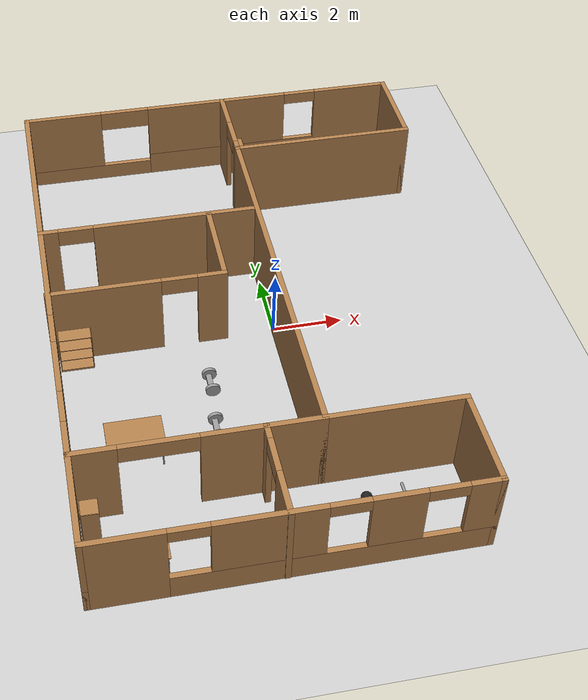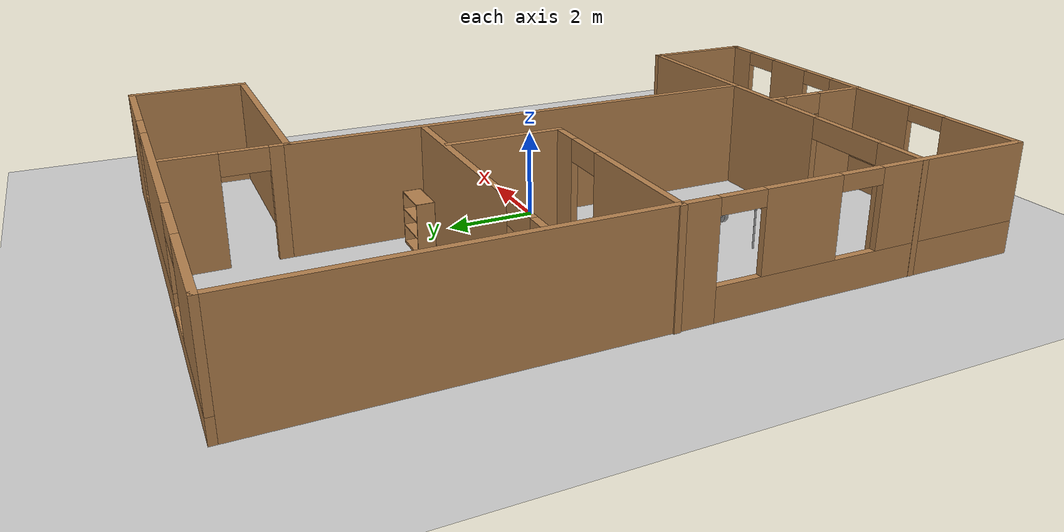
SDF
<sdf version="1.6">
 <world name="default">
  <plugin name="hello" filename="libhello.so"/>
  <light name="sun" type="directional">
   <pose>0 0 10 0 -0 0</pose>
   <diffuse>0.8 0.8 0.8 1</diffuse>
   <specular>0.2 0.2 0.2 1</specular>
   <attenuation>
    <range>1000</range>
    <constant>0.9</constant>
    <linear>0.01</linear>
    <quadratic>0.001</quadratic>
   </attenuation>
   <direction>-0.5 0.1 -0.9</direction>
  </light>
  <model name="ground_plane">
   <static>1</static>
   <link name="link">
    <collision name="collision">
     <geometry><plane><normal>0 0 1</normal><size>100 100</size></plane></geometry>
     <surface><friction><ode><mu>100</mu><mu2>50</mu2></ode></friction></surface>
    </collision>
    <visual name="visual">
     <cast_shadows>0</cast_shadows>
     <geometry><plane><normal>0 0 1</normal><size>100 100</size></plane></geometry>
     <material>
      <script><uri>file://media/materials/scripts/gazebo.material</uri><name>Gazebo/Grey</name></script>
     </material>
    </visual>
   </link>
  </model>
  <gravity>0 0 -9.8</gravity>
  <magnetic_field>6e-06 2.3e-05 -4.2e-05</magnetic_field>
  <atmosphere type="adiabatic"/>
  <physics name="default_physics" default="0" type="ode">
   <max_step_size>0.001</max_step_size>
   <real_time_factor>1</real_time_factor>
   <real_time_update_rate>1000</real_time_update_rate>
  </physics>
  <scene><ambient>0.4 0.4 0.4 1</ambient><background>0.7 0.7 0.7 1</background><shadows>1</shadows></scene>
  <spherical_coordinates>
   <surface_model>EARTH_WGS84</surface_model>
   <latitude_deg>0</latitude_deg>
   <longitude_deg>0</longitude_deg>
   <elevation>0</elevation>
   <heading_deg>0</heading_deg>
  </spherical_coordinates>
  <model name="Building">
   <pose>-0.466 -0.083499 0 0 -0 0</pose>
   <link name="Wall_35">
    <pose>-0.859 -8.1425 0 0 -0 0</pose>
    <visual name="Wall_35_Visual_0">
     <pose>-3.97971 0 1.25 0 -0 0</pose>
     <geometry><box><size>2.04059 0.15 2.5</size></box></geometry>
     <material>
      <script><uri>file://media/materials/scripts/gazebo.material</uri><name>Gazebo/Wood</name></script>
      <ambient>0.996078 0.47451 0.0196078 1</ambient>
     </material>
     <meta><layer>0</layer></meta>
    </visual>
    <collision name="Wall_35_Collision_0">
     <geometry><box><size>2.04059 0.15 2.5</size></box></geometry>
     <pose>-3.97971 0 1.25 0 -0 0</pose>
    </collision>
    <visual name="Wall_35_Visual_1">
     <pose>1.02029 0 0.375 0 -0 0</pose>
     <geometry><box><size>7.95941 0.15 0.75</size></box></geometry>
     <material>
      <script><uri>file://media/materials/scripts/gazebo.material</uri><name>Gazebo/Wood</name></script>
      <ambient>0.996078 0.47451 0.0196078 1</ambient>
     </material>
     <meta><layer>0</layer></meta>
    </visual>
    <collision name="Wall_35_Collision_1">
     <geometry><box><size>7.95941 0.15 0.75</size></box></geometry>
     <pose>1.02029 0 0.375 0 -0 0</pose>
    </collision>
    <visual name="Wall_35_Visual_2">
     <pose>-0.589488 0 1.625 0 -0 0</pose>
     <geometry><box><size>2.73985 0.15 1.75</size></box></geometry>
     <material>
      <script><uri>file://media/materials/scripts/gazebo.material</uri><name>Gazebo/Wood</name></script>
      <ambient>0.996078 0.47451 0.0196078 1</ambient>
     </material>
     <meta><layer>0</layer></meta>
    </visual>
    <collision name="Wall_35_Collision_2">
     <geometry><box><size>2.73985 0.15 1.75</size></box></geometry>
     <pose>-0.589488 0 1.625 0 -0 0</pose>
    </collision>
    <visual name="Wall_35_Visual_3">
     <pose>2.45057 0 1.625 0 -0 0</pose>
     <geometry><box><size>1.34027 0.15 1.75</size></box></geometry>
     <material>
      <script><uri>file://media/materials/scripts/gazebo.material</uri><name>Gazebo/Wood</name></script>
      <ambient>0.996078 0.47451 0.0196078 1</ambient>
     </material>
     <meta><layer>0</layer></meta>
    </visual>
    <collision name="Wall_35_Collision_3">
     <geometry><box><size>1.34027 0.15 1.75</size></box></geometry>
     <pose>2.45057 0 1.625 0 -0 0</pose>
    </collision>
    <visual name="Wall_35_Visual_4">
     <pose>4.56035 0 1.625 0 -0 0</pose>
     <geometry><box><size>0.879297 0.15 1.75</size></box></geometry>
     <material>
      <script><uri>file://media/materials/scripts/gazebo.material</uri><name>Gazebo/Wood</name></script>
      <ambient>0.996078 0.47451 0.0196078 1</ambient>
     </material>
     <meta><layer>0</layer></meta>
    </visual>
    <collision name="Wall_35_Collision_4">
     <geometry><box><size>0.879297 0.15 1.75</size></box></geometry>
     <pose>4.56035 0 1.625 0 -0 0</pose>
    </collision>
    <visual name="Wall_35_Visual_5">
     <pose>-2.45941 0 2.325 0 -0 0</pose>
     <geometry><box><size>1 0.15 0.35</size></box></geometry>
     <material>
      <script><uri>file://media/materials/scripts/gazebo.material</uri><name>Gazebo/Wood</name></script>
      <ambient>0.996078 0.47451 0.0196078 1</ambient>
     </material>
     <meta><layer>0</layer></meta>
    </visual>
    <collision name="Wall_35_Collision_5">
     <geometry><box><size>1 0.15 0.35</size></box></geometry>
     <pose>-2.45941 0 2.325 0 -0 0</pose>
    </collision>
    <visual name="Wall_35_Visual_6">
     <pose>1.28044 0 2.325 0 -0 0</pose>
     <geometry><box><size>1 0.15 0.35</size></box></geometry>
     <material>
      <script><uri>file://media/materials/scripts/gazebo.material</uri><name>Gazebo/Wood</name></script>
      <ambient>0.996078 0.47451 0.0196078 1</ambient>
     </material>
     <meta><layer>0</layer></meta>
    </visual>
    <collision name="Wall_35_Collision_6">
     <geometry><box><size>1 0.15 0.35</size></box></geometry>
     <pose>1.28044 0 2.325 0 -0 0</pose>
    </collision>
    <visual name="Wall_35_Visual_7">
     <pose>3.6207 0 2.325 0 -0 0</pose>
     <geometry><box><size>1 0.15 0.35</size></box></geometry>
     <material>
      <script><uri>file://media/materials/scripts/gazebo.material</uri><name>Gazebo/Wood</name></script>
      <ambient>0.996078 0.47451 0.0196078 1</ambient>
     </material>
     <meta><layer>0</layer></meta>
    </visual>
    <collision name="Wall_35_Collision_7">
     <geometry><box><size>1 0.15 0.35</size></box></geometry>
     <pose>3.6207 0 2.325 0 -0 0</pose>
    </collision>
   </link>
   <link name="Wall_36">
    <collision name="Wall_36_Collision">
     <geometry><box><size>2.75 0.15 2.5</size></box></geometry>
     <pose>0 0 1.25 0 -0 0</pose>
    </collision>
    <visual name="Wall_36_Visual">
     <pose>0 0 1.25 0 -0 0</pose>
     <geometry><box><size>2.75 0.15 2.5</size></box></geometry>
     <material>
      <script><uri>file://media/materials/scripts/gazebo.material</uri><name>Gazebo/Wood</name></script>
      <ambient>0.996078 0.47451 0.0196078 1</ambient>
     </material>
     <meta><layer>0</layer></meta>
    </visual>
    <pose>4.066 -6.8425 0 0 -0 1.5708</pose>
   </link>
   <link name="Wall_37">
    <collision name="Wall_37_Collision">
     <geometry><box><size>3.75 0.15 2.5</size></box></geometry>
     <pose>0 0 1.25 0 -0 0</pose>
    </collision>
    <visual name="Wall_37_Visual">
     <pose>0 0 1.25 0 -0 0</pose>
     <geometry><box><size>3.75 0.15 2.5</size></box></geometry>
     <material>
      <script><uri>file://media/materials/scripts/gazebo.material</uri><name>Gazebo/Wood</name></script>
      <ambient>0.996078 0.47451 0.0196078 1</ambient>
     </material>
     <meta><layer>0</layer></meta>
    </visual>
    <pose>2.266 -5.5425 0 0 -0 3.14159</pose>
   </link>
   <link name="Wall_38">
    <collision name="Wall_38_Collision">
     <geometry><box><size>11.25 0.15 2.5</size></box></geometry>
     <pose>0 0 1.25 0 -0 0</pose>
    </collision>
    <visual name="Wall_38_Visual">
     <pose>0 0 1.25 0 -0 0</pose>
     <geometry><box><size>11.25 0.15 2.5</size></box></geometry>
     <material>
      <script><uri>file://media/materials/scripts/gazebo.material</uri><name>Gazebo/Wood</name></script>
      <ambient>0.996078 0.47451 0.0196078 1</ambient>
     </material>
     <meta><layer>0</layer></meta>
    </visual>
    <pose>0.466 0.007499 0 0 -0 1.5708</pose>
   </link>
   <link name="Wall_39">
    <collision name="Wall_39_Collision">
     <geometry><box><size>5.5 0.15 2.5</size></box></geometry>
     <pose>0 0 1.25 0 -0 0</pose>
    </collision>
    <visual name="Wall_39_Visual">
     <pose>0 0 1.25 0 -0 0</pose>
     <geometry><box><size>5.5 0.15 2.5</size></box></geometry>
     <material>
      <script><uri>file://media/materials/scripts/gazebo.material</uri><name>Gazebo/Wood</name></script>
      <ambient>0.996078 0.47451 0.0196078 1</ambient>
     </material>
     <meta><layer>0</layer></meta>
    </visual>
    <pose>3.141 5.5575 0 0 -0 0</pose>
   </link>
   <link name="Wall_40">
    <collision name="Wall_40_Collision">
     <geometry><box><size>2.75 0.15 2.5</size></box></geometry>
     <pose>0 0 1.25 0 -0 0</pose>
    </collision>
    <visual name="Wall_40_Visual">
     <pose>0 0 1.25 0 -0 0</pose>
     <geometry><box><size>2.75 0.15 2.5</size></box></geometry>
     <material>
      <script><uri>file://media/materials/scripts/gazebo.material</uri><name>Gazebo/Wood</name></script>
      <ambient>0.996078 0.47451 0.0196078 1</ambient>
     </material>
     <meta><layer>0</layer></meta>
    </visual>
    <pose>5.816 6.8575 0 0 -0 1.5708</pose>
   </link>
   <link name="Wall_41">
    <pose>0.016 8.1575 0 0 -0 3.14159</pose>
    <visual name="Wall_41_Visual_0">
     <pose>-4.68142 0 1.25 0 -0 0</pose>
     <geometry><box><size>2.38717 0.15 2.5</size></box></geometry>
     <material>
      <script><uri>file://media/materials/scripts/gazebo.material</uri><name>Gazebo/Wood</name></script>
      <ambient>0.996078 0.47451 0.0196078 1</ambient>
     </material>
     <meta><layer>0</layer></meta>
    </visual>
    <collision name="Wall_41_Collision_0">
     <geometry><box><size>2.38717 0.15 2.5</size></box></geometry>
     <pose>-4.68142 0 1.25 0 -0 0</pose>
    </collision>
    <visual name="Wall_41_Visual_1">
     <pose>-0.76125 0 0.375 0 -0 0</pose>
     <geometry><box><size>5.45316 0.15 0.75</size></box></geometry>
     <material>
      <script><uri>file://media/materials/scripts/gazebo.material</uri><name>Gazebo/Wood</name></script>
      <ambient>0.996078 0.47451 0.0196078 1</ambient>
     </material>
     <meta><layer>0</layer></meta>
    </visual>
    <collision name="Wall_41_Collision_1">
     <geometry><box><size>5.45316 0.15 0.75</size></box></geometry>
     <pose>-0.76125 0 0.375 0 -0 0</pose>
    </collision>
    <visual name="Wall_41_Visual_2">
     <pose>3.92016 0 0.25 0 -0 0</pose>
     <geometry><box><size>3.90967 0.15 0.5</size></box></geometry>
     <material>
      <script><uri>file://media/materials/scripts/gazebo.material</uri><name>Gazebo/Wood</name></script>
      <ambient>0.996078 0.47451 0.0196078 1</ambient>
     </material>
     <meta><layer>0</layer></meta>
    </visual>
    <collision name="Wall_41_Collision_2">
     <geometry><box><size>3.90967 0.15 0.5</size></box></geometry>
     <pose>3.92016 0 0.25 0 -0 0</pose>
    </collision>
    <visual name="Wall_41_Visual_3">
     <pose>4.67016 0 1.5 0 -0 0</pose>
     <geometry><box><size>2.40967 0.15 2</size></box></geometry>
     <material>
      <script><uri>file://media/materials/scripts/gazebo.material</uri><name>Gazebo/Wood</name></script>
      <ambient>0.996078 0.47451 0.0196078 1</ambient>
     </material>
     <meta><layer>0</layer></meta>
    </visual>
    <collision name="Wall_41_Collision_3">
     <geometry><box><size>2.40967 0.15 2</size></box></geometry>
     <pose>4.67016 0 1.5 0 -0 0</pose>
    </collision>
    <visual name="Wall_41_Visual_4">
     <pose>-0.26125 0 1.625 0 -0 0</pose>
     <geometry><box><size>4.45316 0.15 1.75</size></box></geometry>
     <material>
      <script><uri>file://media/materials/scripts/gazebo.material</uri><name>Gazebo/Wood</name></script>
      <ambient>0.996078 0.47451 0.0196078 1</ambient>
     </material>
     <meta><layer>0</layer></meta>
    </visual>
    <collision name="Wall_41_Collision_4">
     <geometry><box><size>4.45316 0.15 1.75</size></box></geometry>
     <pose>-0.26125 0 1.625 0 -0 0</pose>
    </collision>
    <visual name="Wall_41_Visual_5">
     <pose>2.71533 0 2.2 0 -0 0</pose>
     <geometry><box><size>1.5 0.15 0.6</size></box></geometry>
     <material>
      <script><uri>file://media/materials/scripts/gazebo.material</uri><name>Gazebo/Wood</name></script>
      <ambient>0.996078 0.47451 0.0196078 1</ambient>
     </material>
     <meta><layer>0</layer></meta>
    </visual>
    <collision name="Wall_41_Collision_5">
     <geometry><box><size>1.5 0.15 0.6</size></box></geometry>
     <pose>2.71533 0 2.2 0 -0 0</pose>
    </collision>
    <visual name="Wall_41_Visual_6">
     <pose>-2.98783 0 2.325 0 -0 0</pose>
     <geometry><box><size>1 0.15 0.35</size></box></geometry>
     <material>
      <script><uri>file://media/materials/scripts/gazebo.material</uri><name>Gazebo/Wood</name></script>
      <ambient>0.996078 0.47451 0.0196078 1</ambient>
     </material>
     <meta><layer>0</layer></meta>
    </visual>
    <collision name="Wall_41_Collision_6">
     <geometry><box><size>1 0.15 0.35</size></box></geometry>
     <pose>-2.98783 0 2.325 0 -0 0</pose>
    </collision>
   </link>
   <link name="Wall_42">
    <pose>-5.784 0.007499 0 0 -0 -1.5708</pose>
    <visual name="Wall_42_Visual_0">
     <pose>-3.729 0 1.25 0 -0 0</pose>
     <geometry><box><size>8.992 0.15 2.5</size></box></geometry>
     <material>
      <script><uri>file://media/materials/scripts/gazebo.material</uri><name>Gazebo/Wood</name></script>
      <ambient>0.996078 0.47451 0.0196078 1</ambient>
     </material>
     <meta><layer>0</layer></meta>
    </visual>
    <collision name="Wall_42_Collision_0">
     <geometry><box><size>8.992 0.15 2.5</size></box></geometry>
     <pose>-3.729 0 1.25 0 -0 0</pose>
    </collision>
    <visual name="Wall_42_Visual_1">
     <pose>4.496 0 0.375 0 -0 0</pose>
     <geometry><box><size>7.458 0.15 0.75</size></box></geometry>
     <material>
      <script><uri>file://media/materials/scripts/gazebo.material</uri><name>Gazebo/Wood</name></script>
      <ambient>0.996078 0.47451 0.0196078 1</ambient>
     </material>
     <meta><layer>0</layer></meta>
    </visual>
    <collision name="Wall_42_Collision_1">
     <geometry><box><size>7.458 0.15 0.75</size></box></geometry>
     <pose>4.496 0 0.375 0 -0 0</pose>
    </collision>
    <visual name="Wall_42_Visual_2">
     <pose>2.63915 0 1.625 0 -0 0</pose>
     <geometry><box><size>1.7443 0.15 1.75</size></box></geometry>
     <material>
      <script><uri>file://media/materials/scripts/gazebo.material</uri><name>Gazebo/Wood</name></script>
      <ambient>0.996078 0.47451 0.0196078 1</ambient>
     </material>
     <meta><layer>0</layer></meta>
    </visual>
    <collision name="Wall_42_Collision_2">
     <geometry><box><size>1.7443 0.15 1.75</size></box></geometry>
     <pose>2.63915 0 1.625 0 -0 0</pose>
    </collision>
    <visual name="Wall_42_Visual_3">
     <pose>6.36815 0 1.625 0 -0 0</pose>
     <geometry><box><size>3.7137 0.15 1.75</size></box></geometry>
     <material>
      <script><uri>file://media/materials/scripts/gazebo.material</uri><name>Gazebo/Wood</name></script>
      <ambient>0.996078 0.47451 0.0196078 1</ambient>
     </material>
     <meta><layer>0</layer></meta>
    </visual>
    <collision name="Wall_42_Collision_3">
     <geometry><box><size>3.7137 0.15 1.75</size></box></geometry>
     <pose>6.36815 0 1.625 0 -0 0</pose>
    </collision>
    <visual name="Wall_42_Visual_4">
     <pose>1.267 0 2.325 0 -0 0</pose>
     <geometry><box><size>1 0.15 0.35</size></box></geometry>
     <material>
      <script><uri>file://media/materials/scripts/gazebo.material</uri><name>Gazebo/Wood</name></script>
      <ambient>0.996078 0.47451 0.0196078 1</ambient>
     </material>
     <meta><layer>0</layer></meta>
    </visual>
    <collision name="Wall_42_Collision_4">
     <geometry><box><size>1 0.15 0.35</size></box></geometry>
     <pose>1.267 0 2.325 0 -0 0</pose>
    </collision>
    <visual name="Wall_42_Visual_5">
     <pose>4.0113 0 2.325 0 -0 0</pose>
     <geometry><box><size>1 0.15 0.35</size></box></geometry>
     <material>
      <script><uri>file://media/materials/scripts/gazebo.material</uri><name>Gazebo/Wood</name></script>
      <ambient>0.996078 0.47451 0.0196078 1</ambient>
     </material>
     <meta><layer>0</layer></meta>
    </visual>
    <collision name="Wall_42_Collision_5">
     <geometry><box><size>1 0.15 0.35</size></box></geometry>
     <pose>4.0113 0 2.325 0 -0 0</pose>
    </collision>
   </link>
   <link name="Wall_44">
    <pose>0.466 6.8575 0 0 -0 1.5708</pose>
    <visual name="Wall_44_Visual_0">
     <pose>-1.15301 0 1.25 0 -0 0</pose>
     <geometry><box><size>0.443977 0.15 2.5</size></box></geometry>
     <material>
      <script><uri>file://media/materials/scripts/gazebo.material</uri><name>Gazebo/Wood</name></script>
      <ambient>0.996078 0.47451 0.0196078 1</ambient>
     </material>
     <meta><layer>0</layer></meta>
    </visual>
    <collision name="Wall_44_Collision_0">
     <geometry><box><size>0.443977 0.15 2.5</size></box></geometry>
     <pose>-1.15301 0 1.25 0 -0 0</pose>
    </collision>
    <visual name="Wall_44_Visual_1">
     <pose>0.721988 0 1.25 0 -0 0</pose>
     <geometry><box><size>1.30602 0.15 2.5</size></box></geometry>
     <material>
      <script><uri>file://media/materials/scripts/gazebo.material</uri><name>Gazebo/Wood</name></script>
      <ambient>0.996078 0.47451 0.0196078 1</ambient>
     </material>
     <meta><layer>0</layer></meta>
    </visual>
    <collision name="Wall_44_Collision_1">
     <geometry><box><size>1.30602 0.15 2.5</size></box></geometry>
     <pose>0.721988 0 1.25 0 -0 0</pose>
    </collision>
    <visual name="Wall_44_Visual_2">
     <pose>-0.431023 0 2.25 0 -0 0</pose>
     <geometry><box><size>1 0.15 0.5</size></box></geometry>
     <material>
      <script><uri>file://media/materials/scripts/gazebo.material</uri><name>Gazebo/Wood</name></script>
      <ambient>0.996078 0.47451 0.0196078 1</ambient>
     </material>
     <meta><layer>0</layer></meta>
    </visual>
    <collision name="Wall_44_Collision_2">
     <geometry><box><size>1 0.15 0.5</size></box></geometry>
     <pose>-0.431023 0 2.25 0 -0 0</pose>
    </collision>
   </link>
   <link name="Wall_46">
    <pose>-2.733 2.6255 0 0 -0 0</pose>
    <visual name="Wall_46_Visual_0">
     <pose>-2.84077 0 1.25 0 -0 0</pose>
     <geometry><box><size>0.56845 0.15 2.5</size></box></geometry>
     <material>
      <script><uri>file://media/materials/scripts/gazebo.material</uri><name>Gazebo/Wood</name></script>
      <ambient>0.996078 0.47451 0.0196078 1</ambient>
     </material>
     <meta><layer>0</layer></meta>
    </visual>
    <collision name="Wall_46_Collision_0">
     <geometry><box><size>0.56845 0.15 2.5</size></box></geometry>
     <pose>-2.84077 0 1.25 0 -0 0</pose>
    </collision>
    <visual name="Wall_46_Visual_1">
     <pose>0.784225 0 1.25 0 -0 0</pose>
     <geometry><box><size>4.68155 0.15 2.5</size></box></geometry>
     <material>
      <script><uri>file://media/materials/scripts/gazebo.material</uri><name>Gazebo/Wood</name></script>
      <ambient>0.996078 0.47451 0.0196078 1</ambient>
     </material>
     <meta><layer>0</layer></meta>
    </visual>
    <collision name="Wall_46_Collision_1">
     <geometry><box><size>4.68155 0.15 2.5</size></box></geometry>
     <pose>0.784225 0 1.25 0 -0 0</pose>
    </collision>
    <visual name="Wall_46_Visual_2">
     <pose>-2.05655 0 2.25 0 -0 0</pose>
     <geometry><box><size>1 0.15 0.5</size></box></geometry>
     <material>
      <script><uri>file://media/materials/scripts/gazebo.material</uri><name>Gazebo/Wood</name></script>
      <ambient>0.996078 0.47451 0.0196078 1</ambient>
     </material>
     <meta><layer>0</layer></meta>
    </visual>
    <collision name="Wall_46_Collision_2">
     <geometry><box><size>1 0.15 0.5</size></box></geometry>
     <pose>-2.05655 0 2.25 0 -0 0</pose>
    </collision>
   </link>
   <link name="Wall_48">
    <pose>-3.391 0.046499 0 0 -0 0</pose>
    <visual name="Wall_48_Visual_0">
     <pose>-0.915348 0 1.25 0 -0 0</pose>
     <geometry><box><size>3.1693 0.15 2.5</size></box></geometry>
     <material>
      <script><uri>file://media/materials/scripts/gazebo.material</uri><name>Gazebo/Wood</name></script>
      <ambient>0.996078 0.47451 0.0196078 1</ambient>
     </material>
     <meta><layer>0</layer></meta>
    </visual>
    <collision name="Wall_48_Collision_0">
     <geometry><box><size>3.1693 0.15 2.5</size></box></geometry>
     <pose>-0.915348 0 1.25 0 -0 0</pose>
    </collision>
    <visual name="Wall_48_Visual_1">
     <pose>2.08465 0 1.25 0 -0 0</pose>
     <geometry><box><size>0.830696 0.15 2.5</size></box></geometry>
     <material>
      <script><uri>file://media/materials/scripts/gazebo.material</uri><name>Gazebo/Wood</name></script>
      <ambient>0.996078 0.47451 0.0196078 1</ambient>
     </material>
     <meta><layer>0</layer></meta>
    </visual>
    <collision name="Wall_48_Collision_1">
     <geometry><box><size>0.830696 0.15 2.5</size></box></geometry>
     <pose>2.08465 0 1.25 0 -0 0</pose>
    </collision>
    <visual name="Wall_48_Visual_2">
     <pose>1.1693 0 2.25 0 -0 0</pose>
     <geometry><box><size>1 0.15 0.5</size></box></geometry>
     <material>
      <script><uri>file://media/materials/scripts/gazebo.material</uri><name>Gazebo/Wood</name></script>
      <ambient>0.996078 0.47451 0.0196078 1</ambient>
     </material>
     <meta><layer>0</layer></meta>
    </visual>
    <collision name="Wall_48_Collision_2">
     <geometry><box><size>1 0.15 0.5</size></box></geometry>
     <pose>1.1693 0 2.25 0 -0 0</pose>
    </collision>
   </link>
   <link name="Wall_49">
    <collision name="Wall_49_Collision">
     <geometry><box><size>2.66373 0.15 2.5</size></box></geometry>
     <pose>0 0 1.25 0 -0 0</pose>
    </collision>
    <visual name="Wall_49_Visual">
     <pose>0 0 1.25 0 -0 0</pose>
     <geometry><box><size>2.66373 0.15 2.5</size></box></geometry>
     <material>
      <script><uri>file://media/materials/scripts/gazebo.material</uri><name>Gazebo/Wood</name></script>
      <ambient>0.996078 0.47451 0.0196078 1</ambient>
     </material>
     <meta><layer>0</layer></meta>
    </visual>
    <pose>-0.964 1.3035 0 0 -0 1.5692</pose>
   </link>
   <link name="Wall_51">
    <pose>-2.6615 -5.5425 0 0 -0 0</pose>
    <visual name="Wall_51_Visual_0">
     <pose>-2.57774 0 1.25 0 -0 0</pose>
     <geometry><box><size>1.24958 0.15 2.5</size></box></geometry>
     <material>
      <script><uri>file://media/materials/scripts/gazebo.material</uri><name>Gazebo/Wood</name></script>
      <ambient>0.996078 0.47451 0.0196078 1</ambient>
     </material>
     <meta><layer>0</layer></meta>
    </visual>
    <collision name="Wall_51_Collision_0">
     <geometry><box><size>1.24958 0.15 2.5</size></box></geometry>
     <pose>-2.57774 0 1.25 0 -0 0</pose>
    </collision>
    <visual name="Wall_51_Visual_1">
     <pose>1.62479 0 1.25 0 -0 0</pose>
     <geometry><box><size>3.15547 0.15 2.5</size></box></geometry>
     <material>
      <script><uri>file://media/materials/scripts/gazebo.material</uri><name>Gazebo/Wood</name></script>
      <ambient>0.996078 0.47451 0.0196078 1</ambient>
     </material>
     <meta><layer>0</layer></meta>
    </visual>
    <collision name="Wall_51_Collision_1">
     <geometry><box><size>3.15547 0.15 2.5</size></box></geometry>
     <pose>1.62479 0 1.25 0 -0 0</pose>
    </collision>
    <visual name="Wall_51_Visual_2">
     <pose>-0.952945 0 2.25 0 -0 0</pose>
     <geometry><box><size>2 0.15 0.5</size></box></geometry>
     <material>
      <script><uri>file://media/materials/scripts/gazebo.material</uri><name>Gazebo/Wood</name></script>
      <ambient>0.996078 0.47451 0.0196078 1</ambient>
     </material>
     <meta><layer>0</layer></meta>
    </visual>
    <collision name="Wall_51_Collision_2">
     <geometry><box><size>2 0.15 0.5</size></box></geometry>
     <pose>-0.952945 0 2.25 0 -0 0</pose>
    </collision>
   </link>
   <link name="Wall_53">
    <pose>-0.99 -6.8575 0 0 -0 -1.5708</pose>
    <visual name="Wall_53_Visual_0">
     <pose>-1.14437 0 1.25 0 -0 0</pose>
     <geometry><box><size>0.461266 0.15 2.5</size></box></geometry>
     <material>
      <script><uri>file://media/materials/scripts/gazebo.material</uri><name>Gazebo/Wood</name></script>
      <ambient>0.996078 0.47451 0.0196078 1</ambient>
     </material>
     <meta><layer>0</layer></meta>
    </visual>
    <collision name="Wall_53_Collision_0">
     <geometry><box><size>0.461266 0.15 2.5</size></box></geometry>
     <pose>-1.14437 0 1.25 0 -0 0</pose>
    </collision>
    <visual name="Wall_53_Visual_1">
     <pose>0.730633 0 1.25 0 -0 0</pose>
     <geometry><box><size>1.28873 0.15 2.5</size></box></geometry>
     <material>
      <script><uri>file://media/materials/scripts/gazebo.material</uri><name>Gazebo/Wood</name></script>
      <ambient>0.996078 0.47451 0.0196078 1</ambient>
     </material>
     <meta><layer>0</layer></meta>
    </visual>
    <collision name="Wall_53_Collision_1">
     <geometry><box><size>1.28873 0.15 2.5</size></box></geometry>
     <pose>0.730633 0 1.25 0 -0 0</pose>
    </collision>
    <visual name="Wall_53_Visual_2">
     <pose>-0.413734 0 2.25 0 -0 0</pose>
     <geometry><box><size>1 0.15 0.5</size></box></geometry>
     <material>
      <script><uri>file://media/materials/scripts/gazebo.material</uri><name>Gazebo/Wood</name></script>
      <ambient>0.996078 0.47451 0.0196078 1</ambient>
     </material>
     <meta><layer>0</layer></meta>
    </visual>
    <collision name="Wall_53_Collision_2">
     <geometry><box><size>1 0.15 0.5</size></box></geometry>
     <pose>-0.413734 0 2.25 0 -0 0</pose>
    </collision>
   </link>
   <static>1</static>
  </model>
  <model name="TwoWheeledRobot">
   <link name="link_0">
    <inertial>
     <mass>1</mass>
     <inertia>
      <ixx>0.166667</ixx>
      <ixy>0</ixy>
      <ixz>0</ixz>
      <iyy>0.166667</iyy>
      <iyz>0</iyz>
      <izz>0.166667</izz>
     </inertia>
     <pose>0 0 0.2 0 -0 0</pose>
    </inertial>
    <pose>-0.021667 0 0 0 -0 0</pose>
    <visual name="visual">
     <geometry><box><size>0.15 0.5 0.1</size></box></geometry>
     <material>
      <lighting>1</lighting>
      <script><uri>file://media/materials/scripts/gazebo.material</uri><name>Gazebo/Grey</name></script>
      <shader type="pixel"><normal_map>__default__</normal_map></shader>
      <ambient>0.3 0.3 0.3 1</ambient>
      <diffuse>0.7 0.7 0.7 1</diffuse>
      <specular>0.01 0.01 0.01 1</specular>
      <emissive>0 0 0 1</emissive>
     </material>
    </visual>
    <collision name="collision">
     <geometry><box><size>0.15 0.5 0.1</size></box></geometry>
     <surface>
      <friction>
       <ode><mu>1</mu><mu2>1</mu2><fdir1>0 0 0</fdir1><slip1>0</slip1><slip2>0</slip2></ode>
       <torsional>
        <coefficient>1</coefficient>
        <patch_radius>0</patch_radius>
        <surface_radius>0</surface_radius>
        <use_patch_radius>1</use_patch_radius>
        <ode><slip>0</slip></ode>
       </torsional>
      </friction>
      <bounce><restitution_coefficient>0</restitution_coefficient><threshold>1e+06</threshold></bounce>
      <contact>
       <collide_without_contact>0</collide_without_contact>
       <collide_without_contact_bitmask>1</collide_without_contact_bitmask>
       <collide_bitmask>1</collide_bitmask>
       <ode>
        <soft_cfm>0</soft_cfm>
        <soft_erp>0.2</soft_erp>
        <kp>1e+13</kp>
        <kd>1</kd>
        <max_vel>0.01</max_vel>
        <min_depth>0</min_depth>
       </ode>
       <bullet>
        <split_impulse>1</split_impulse>
        <split_impulse_penetration_threshold>-0.01</split_impulse_penetration_threshold>
        <soft_cfm>0</soft_cfm>
        <soft_erp>0.2</soft_erp>
        <kp>1e+13</kp>
        <kd>1</kd>
       </bullet>
      </contact>
     </surface>
    </collision>
   </link>
   <link name="link_1">
    <inertial>
     <mass>1</mass>
     <inertia><ixx>0.145833</ixx><ixy>0</ixy><ixz>0</ixz><iyy>0.145833</iyy><iyz>0</iyz><izz>0.125</izz></inertia>
    </inertial>
    <pose>0.010833 -0.300019 0 1.5707 -0 0</pose>
    <visual name="visual">
     <geometry><cylinder><radius>0.2</radius><length>0.1</length></cylinder></geometry>
     <material>
      <lighting>1</lighting>
      <script><uri>file://media/materials/scripts/gazebo.material</uri><name>Gazebo/Grey</name></script>
      <shader type="pixel"><normal_map>__default__</normal_map></shader>
      <ambient>0.3 0.3 0.3 1</ambient>
      <diffuse>0.7 0.7 0.7 1</diffuse>
      <specular>0.01 0.01 0.01 1</specular>
      <emissive>0 0 0 1</emissive>
     </material>
    </visual>
    <collision name="collision">
     <geometry><cylinder><radius>0.2</radius><length>0.1</length></cylinder></geometry>
     <surface>
      <friction>
       <ode><mu>1</mu><mu2>1</mu2><fdir1>0 0 0</fdir1><slip1>0</slip1><slip2>0</slip2></ode>
       <torsional>
        <coefficient>1</coefficient>
        <patch_radius>0</patch_radius>
        <surface_radius>0</surface_radius>
        <use_patch_radius>1</use_patch_radius>
        <ode><slip>0</slip></ode>
       </torsional>
      </friction>
      <bounce><restitution_coefficient>0</restitution_coefficient><threshold>1e+06</threshold></bounce>
      <contact>
       <collide_without_contact>0</collide_without_contact>
       <collide_without_contact_bitmask>1</collide_without_contact_bitmask>
       <collide_bitmask>1</collide_bitmask>
       <ode>
        <soft_cfm>0</soft_cfm>
        <soft_erp>0.2</soft_erp>
        <kp>1e+13</kp>
        <kd>1</kd>
        <max_vel>0.01</max_vel>
        <min_depth>0</min_depth>
       </ode>
       <bullet>
        <split_impulse>1</split_impulse>
        <split_impulse_penetration_threshold>-0.01</split_impulse_penetration_threshold>
        <soft_cfm>0</soft_cfm>
        <soft_erp>0.2</soft_erp>
        <kp>1e+13</kp>
        <kd>1</kd>
       </bullet>
      </contact>
     </surface>
    </collision>
   </link>
   <link name="link_1_clone">
    <inertial>
     <mass>1</mass>
     <inertia><ixx>0.145833</ixx><ixy>0</ixy><ixz>0</ixz><iyy>0.145833</iyy><iyz>0</iyz><izz>0.125</izz></inertia>
    </inertial>
    <pose>0.010833 0.300019 0 1.5707 -0 0</pose>
    <visual name="visual">
     <geometry><cylinder><radius>0.2</radius><length>0.1</length></cylinder></geometry>
     <material>
      <lighting>1</lighting>
      <script><uri>file://media/materials/scripts/gazebo.material</uri><name>Gazebo/Grey</name></script>
      <shader type="pixel"><normal_map>__default__</normal_map></shader>
      <ambient>0.3 0.3 0.3 1</ambient>
      <diffuse>0.7 0.7 0.7 1</diffuse>
      <specular>0.01 0.01 0.01 1</specular>
      <emissive>0 0 0 1</emissive>
     </material>
    </visual>
    <collision name="collision">
     <geometry><cylinder><radius>0.2</radius><length>0.1</length></cylinder></geometry>
     <surface>
      <friction>
       <ode><mu>1</mu><mu2>1</mu2><fdir1>0 0 0</fdir1><slip1>0</slip1><slip2>0</slip2></ode>
       <torsional>
        <coefficient>1</coefficient>
        <patch_radius>0</patch_radius>
        <surface_radius>0</surface_radius>
        <use_patch_radius>1</use_patch_radius>
        <ode><slip>0</slip></ode>
       </torsional>
      </friction>
      <bounce><restitution_coefficient>0</restitution_coefficient><threshold>1e+06</threshold></bounce>
      <contact>
       <collide_without_contact>0</collide_without_contact>
       <collide_without_contact_bitmask>1</collide_without_contact_bitmask>
       <collide_bitmask>1</collide_bitmask>
       <ode>
        <soft_cfm>0</soft_cfm>
        <soft_erp>0.2</soft_erp>
        <kp>1e+13</kp>
        <kd>1</kd>
        <max_vel>0.01</max_vel>
        <min_depth>0</min_depth>
       </ode>
       <bullet>
        <split_impulse>1</split_impulse>
        <split_impulse_penetration_threshold>-0.01</split_impulse_penetration_threshold>
        <soft_cfm>0</soft_cfm>
        <soft_erp>0.2</soft_erp>
        <kp>1e+13</kp>
        <kd>1</kd>
       </bullet>
      </contact>
     </surface>
    </collision>
   </link>
   <joint name="link_0_JOINT_0" type="revolute">
    <parent>link_0</parent>
    <child>link_1</child>
    <axis>
     <xyz>0 0 1</xyz>
     <use_parent_model_frame>0</use_parent_model_frame>
     <limit>
      <lower>-1.79769e+308</lower>
      <upper>1.79769e+308</upper>
      <effort>-1</effort>
      <velocity>-1</velocity>
     </limit>
     <dynamics>
      <spring_reference>0</spring_reference>
      <spring_stiffness>0</spring_stiffness>
      <damping>0</damping>
     </dynamics>
    </axis>
    <physics>
     <ode><limit><cfm>0</cfm><erp>0.2</erp></limit><suspension><cfm>0</cfm><erp>0.2</erp></suspension></ode>
    </physics>
   </joint>
   <joint name="link_0_JOINT_1" type="revolute">
    <parent>link_0</parent>
    <child>link_1_clone</child>
    <axis>
     <xyz>0 0 1</xyz>
     <use_parent_model_frame>0</use_parent_model_frame>
     <limit>
      <lower>-1.79769e+308</lower>
      <upper>1.79769e+308</upper>
      <effort>-1</effort>
      <velocity>-1</velocity>
     </limit>
     <dynamics>
      <spring_reference>0</spring_reference>
      <spring_stiffness>0</spring_stiffness>
      <damping>0</damping>
     </dynamics>
    </axis>
    <physics>
     <ode><limit><cfm>0</cfm><erp>0.2</erp></limit><suspension><cfm>0</cfm><erp>0.2</erp></suspension></ode>
    </physics>
   </joint>
   <static>0</static>
   <pose>-2.17333 -1.88061 0.2 0 -0 0</pose>
  </model>
  <model name="TwoWheeledRobot_0">
   <link name="link_0">
    <inertial>
     <mass>1</mass>
     <inertia>
      <ixx>0.166667</ixx>
      <ixy>0</ixy>
      <ixz>0</ixz>
      <iyy>0.166667</iyy>
      <iyz>0</iyz>
      <izz>0.166667</izz>
     </inertia>
     <pose>0 0 0.2 0 -0 0</pose>
    </inertial>
    <pose>-0.021667 0 0 0 -0 0</pose>
    <visual name="visual">
     <geometry><box><size>0.15 0.5 0.1</size></box></geometry>
     <material>
      <lighting>1</lighting>
      <script><uri>file://media/materials/scripts/gazebo.material</uri><name>Gazebo/Grey</name></script>
      <shader type="pixel"><normal_map>__default__</normal_map></shader>
      <ambient>0.3 0.3 0.3 1</ambient>
      <diffuse>0.7 0.7 0.7 1</diffuse>
      <specular>0.01 0.01 0.01 1</specular>
      <emissive>0 0 0 1</emissive>
     </material>
    </visual>
    <collision name="collision">
     <geometry><box><size>0.15 0.5 0.1</size></box></geometry>
     <surface>
      <friction>
       <ode><mu>1</mu><mu2>1</mu2><fdir1>0 0 0</fdir1><slip1>0</slip1><slip2>0</slip2></ode>
       <torsional>
        <coefficient>1</coefficient>
        <patch_radius>0</patch_radius>
        <surface_radius>0</surface_radius>
        <use_patch_radius>1</use_patch_radius>
        <ode><slip>0</slip></ode>
       </torsional>
      </friction>
      <bounce><restitution_coefficient>0</restitution_coefficient><threshold>1e+06</threshold></bounce>
      <contact>
       <collide_without_contact>0</collide_without_contact>
       <collide_without_contact_bitmask>1</collide_without_contact_bitmask>
       <collide_bitmask>1</collide_bitmask>
       <ode>
        <soft_cfm>0</soft_cfm>
        <soft_erp>0.2</soft_erp>
        <kp>1e+13</kp>
        <kd>1</kd>
        <max_vel>0.01</max_vel>
        <min_depth>0</min_depth>
       </ode>
       <bullet>
        <split_impulse>1</split_impulse>
        <split_impulse_penetration_threshold>-0.01</split_impulse_penetration_threshold>
        <soft_cfm>0</soft_cfm>
        <soft_erp>0.2</soft_erp>
        <kp>1e+13</kp>
        <kd>1</kd>
       </bullet>
      </contact>
     </surface>
    </collision>
   </link>
   <link name="link_1">
    <inertial>
     <mass>1</mass>
     <inertia><ixx>0.145833</ixx><ixy>0</ixy><ixz>0</ixz><iyy>0.145833</iyy><iyz>0</iyz><izz>0.125</izz></inertia>
    </inertial>
    <pose>0.010833 -0.300019 0 1.5707 -0 0</pose>
    <visual name="visual">
     <geometry><cylinder><radius>0.2</radius><length>0.1</length></cylinder></geometry>
     <material>
      <lighting>1</lighting>
      <script><uri>file://media/materials/scripts/gazebo.material</uri><name>Gazebo/Grey</name></script>
      <shader type="pixel"><normal_map>__default__</normal_map></shader>
      <ambient>0.3 0.3 0.3 1</ambient>
      <diffuse>0.7 0.7 0.7 1</diffuse>
      <specular>0.01 0.01 0.01 1</specular>
      <emissive>0 0 0 1</emissive>
     </material>
    </visual>
    <collision name="collision">
     <geometry><cylinder><radius>0.2</radius><length>0.1</length></cylinder></geometry>
     <surface>
      <friction>
       <ode><mu>1</mu><mu2>1</mu2><fdir1>0 0 0</fdir1><slip1>0</slip1><slip2>0</slip2></ode>
       <torsional>
        <coefficient>1</coefficient>
        <patch_radius>0</patch_radius>
        <surface_radius>0</surface_radius>
        <use_patch_radius>1</use_patch_radius>
        <ode><slip>0</slip></ode>
       </torsional>
      </friction>
      <bounce><restitution_coefficient>0</restitution_coefficient><threshold>1e+06</threshold></bounce>
      <contact>
       <collide_without_contact>0</collide_without_contact>
       <collide_without_contact_bitmask>1</collide_without_contact_bitmask>
       <collide_bitmask>1</collide_bitmask>
       <ode>
        <soft_cfm>0</soft_cfm>
        <soft_erp>0.2</soft_erp>
        <kp>1e+13</kp>
        <kd>1</kd>
        <max_vel>0.01</max_vel>
        <min_depth>0</min_depth>
       </ode>
       <bullet>
        <split_impulse>1</split_impulse>
        <split_impulse_penetration_threshold>-0.01</split_impulse_penetration_threshold>
        <soft_cfm>0</soft_cfm>
        <soft_erp>0.2</soft_erp>
        <kp>1e+13</kp>
        <kd>1</kd>
       </bullet>
      </contact>
     </surface>
    </collision>
   </link>
   <link name="link_1_clone">
    <inertial>
     <mass>1</mass>
     <inertia><ixx>0.145833</ixx><ixy>0</ixy><ixz>0</ixz><iyy>0.145833</iyy><iyz>0</iyz><izz>0.125</izz></inertia>
    </inertial>
    <pose>0.010833 0.300019 0 1.5707 -0 0</pose>
    <visual name="visual">
     <geometry><cylinder><radius>0.2</radius><length>0.1</length></cylinder></geometry>
     <material>
      <lighting>1</lighting>
      <script><uri>file://media/materials/scripts/gazebo.material</uri><name>Gazebo/Grey</name></script>
      <shader type="pixel"><normal_map>__default__</normal_map></shader>
      <ambient>0.3 0.3 0.3 1</ambient>
      <diffuse>0.7 0.7 0.7 1</diffuse>
      <specular>0.01 0.01 0.01 1</specular>
      <emissive>0 0 0 1</emissive>
     </material>
    </visual>
    <collision name="collision">
     <geometry><cylinder><radius>0.2</radius><length>0.1</length></cylinder></geometry>
     <surface>
      <friction>
       <ode><mu>1</mu><mu2>1</mu2><fdir1>0 0 0</fdir1><slip1>0</slip1><slip2>0</slip2></ode>
       <torsional>
        <coefficient>1</coefficient>
        <patch_radius>0</patch_radius>
        <surface_radius>0</surface_radius>
        <use_patch_radius>1</use_patch_radius>
        <ode><slip>0</slip></ode>
       </torsional>
      </friction>
      <bounce><restitution_coefficient>0</restitution_coefficient><threshold>1e+06</threshold></bounce>
      <contact>
       <collide_without_contact>0</collide_without_contact>
       <collide_without_contact_bitmask>1</collide_without_contact_bitmask>
       <collide_bitmask>1</collide_bitmask>
       <ode>
        <soft_cfm>0</soft_cfm>
        <soft_erp>0.2</soft_erp>
        <kp>1e+13</kp>
        <kd>1</kd>
        <max_vel>0.01</max_vel>
        <min_depth>0</min_depth>
       </ode>
       <bullet>
        <split_impulse>1</split_impulse>
        <split_impulse_penetration_threshold>-0.01</split_impulse_penetration_threshold>
        <soft_cfm>0</soft_cfm>
        <soft_erp>0.2</soft_erp>
        <kp>1e+13</kp>
        <kd>1</kd>
       </bullet>
      </contact>
     </surface>
    </collision>
   </link>
   <joint name="link_0_JOINT_0" type="revolute">
    <parent>link_0</parent>
    <child>link_1</child>
    <axis>
     <xyz>0 0 1</xyz>
     <use_parent_model_frame>0</use_parent_model_frame>
     <limit>
      <lower>-1.79769e+308</lower>
      <upper>1.79769e+308</upper>
      <effort>-1</effort>
      <velocity>-1</velocity>
     </limit>
     <dynamics>
      <spring_reference>0</spring_reference>
      <spring_stiffness>0</spring_stiffness>
      <damping>0</damping>
     </dynamics>
    </axis>
    <physics>
     <ode><limit><cfm>0</cfm><erp>0.2</erp></limit><suspension><cfm>0</cfm><erp>0.2</erp></suspension></ode>
    </physics>
   </joint>
   <joint name="link_0_JOINT_1" type="revolute">
    <parent>link_0</parent>
    <child>link_1_clone</child>
    <axis>
     <xyz>0 0 1</xyz>
     <use_parent_model_frame>0</use_parent_model_frame>
     <limit>
      <lower>-1.79769e+308</lower>
      <upper>1.79769e+308</upper>
      <effort>-1</effort>
      <velocity>-1</velocity>
     </limit>
     <dynamics>
      <spring_reference>0</spring_reference>
      <spring_stiffness>0</spring_stiffness>
      <damping>0</damping>
     </dynamics>
    </axis>
    <physics>
     <ode><limit><cfm>0</cfm><erp>0.2</erp></limit><suspension><cfm>0</cfm><erp>0.2</erp></suspension></ode>
    </physics>
   </joint>
   <static>0</static>
   <pose>-2.29318 -3.50931 0.2 0 -0 0</pose>
  </model>
  <model name="cabinet">
   <static>1</static>
   <link name="cabinet_bottom_plate">
    <inertial>
     <pose>0 0 -1 0 -0 0</pose>
     <inertia><ixx>2.05</ixx><ixy>0</ixy><ixz>0</ixz><iyy>2.05</iyy><iyz>0</iyz><izz>2.05</izz></inertia>
     <mass>25</mass>
    </inertial>
    <collision name="cabinet_bottom_plate_geom">
     <pose>0 0 0.01 0 -0 0</pose>
     <geometry><box><size>0.45 0.45 0.02</size></box></geometry>
    </collision>
    <visual name="cabinet_bottom_plate_geom_visual">
     <pose>0 0 0.01 0 -0 0</pose>
     <geometry><box><size>0.45 0.45 0.02</size></box></geometry>
     <material>
      <script><uri>file://media/materials/scripts/gazebo.material</uri><name>Gazebo/Wood</name></script>
     </material>
    </visual>
    <collision name="cabinet_bottom_plate_geom_cabinet_back_plate">
     <pose>0.235 0 0.51 0 -0 0</pose>
     <geometry><box><size>0.02 0.45 1.02</size></box></geometry>
    </collision>
    <visual name="cabinet_bottom_plate_geom_cabinet_back_plate_visual">
     <pose>0.235 0 0.51 0 -0 0</pose>
     <geometry><box><size>0.02 0.45 1.02</size></box></geometry>
     <material>
      <script><uri>file://media/materials/scripts/gazebo.material</uri><name>Gazebo/Wood</name></script>
     </material>
    </visual>
    <collision name="cabinet_bottom_plate_geom_cabinet_left_plate">
     <pose>0 0.235 0.51 0 -0 0</pose>
     <geometry><box><size>0.45 0.02 1.02</size></box></geometry>
    </collision>
    <visual name="cabinet_bottom_plate_geom_cabinet_left_plate_visual">
     <pose>0 0.235 0.51 0 -0 0</pose>
     <geometry><box><size>0.45 0.02 1.02</size></box></geometry>
     <material>
      <script><uri>file://media/materials/scripts/gazebo.material</uri><name>Gazebo/Wood</name></script>
     </material>
    </visual>
    <collision name="cabinet_bottom_plate_geom_cabinet_middle_plate">
     <pose>0 0 0.51 0 -0 0</pose>
     <geometry><box><size>0.45 0.45 0.02</size></box></geometry>
    </collision>
    <visual name="cabinet_bottom_plate_geom_cabinet_middle_plate_visual">
     <pose>0 0 0.51 0 -0 0</pose>
     <geometry><box><size>0.45 0.45 0.02</size></box></geometry>
     <material>
      <script><uri>file://media/materials/scripts/gazebo.material</uri><name>Gazebo/Wood</name></script>
     </material>
    </visual>
    <collision name="cabinet_bottom_plate_geom_cabinet_right_plate">
     <pose>0 -0.235 0.51 0 -0 0</pose>
     <geometry><box><size>0.45 0.02 1.02</size></box></geometry>
    </collision>
    <visual name="cabinet_bottom_plate_geom_cabinet_right_plate_visual">
     <pose>0 -0.235 0.51 0 -0 0</pose>
     <geometry><box><size>0.45 0.02 1.02</size></box></geometry>
     <material>
      <script><uri>file://media/materials/scripts/gazebo.material</uri><name>Gazebo/Wood</name></script>
     </material>
    </visual>
    <collision name="cabinet_bottom_plate_geom_cabinet_top_plate">
     <pose>0 0 1.01 0 -0 0</pose>
     <geometry><box><size>0.45 0.45 0.02</size></box></geometry>
    </collision>
    <visual name="cabinet_bottom_plate_geom_cabinet_top_plate_visual">
     <pose>0 0 1.01 0 -0 0</pose>
     <geometry><box><size>0.45 0.45 0.02</size></box></geometry>
     <material>
      <script><uri>file://media/materials/scripts/gazebo.material</uri><name>Gazebo/Wood</name></script>
     </material>
    </visual>
   </link>
   <pose>-5.90656 -6.11318 0 0 -0 3.1347</pose>
  </model>
  <model name="cabinet_0">
   <static>1</static>
   <link name="cabinet_bottom_plate">
    <inertial>
     <pose>0 0 -1 0 -0 0</pose>
     <inertia><ixx>2.05</ixx><ixy>0</ixy><ixz>0</ixz><iyy>2.05</iyy><iyz>0</iyz><izz>2.05</izz></inertia>
     <mass>25</mass>
    </inertial>
    <collision name="cabinet_bottom_plate_geom">
     <pose>0 0 0.01 0 -0 0</pose>
     <geometry><box><size>0.45 0.45 0.02</size></box></geometry>
    </collision>
    <visual name="cabinet_bottom_plate_geom_visual">
     <pose>0 0 0.01 0 -0 0</pose>
     <geometry><box><size>0.45 0.45 0.02</size></box></geometry>
     <material>
      <script><uri>file://media/materials/scripts/gazebo.material</uri><name>Gazebo/Wood</name></script>
     </material>
    </visual>
    <collision name="cabinet_bottom_plate_geom_cabinet_back_plate">
     <pose>0.235 0 0.51 0 -0 0</pose>
     <geometry><box><size>0.02 0.45 1.02</size></box></geometry>
    </collision>
    <visual name="cabinet_bottom_plate_geom_cabinet_back_plate_visual">
     <pose>0.235 0 0.51 0 -0 0</pose>
     <geometry><box><size>0.02 0.45 1.02</size></box></geometry>
     <material>
      <script><uri>file://media/materials/scripts/gazebo.material</uri><name>Gazebo/Wood</name></script>
     </material>
    </visual>
    <collision name="cabinet_bottom_plate_geom_cabinet_left_plate">
     <pose>0 0.235 0.51 0 -0 0</pose>
     <geometry><box><size>0.45 0.02 1.02</size></box></geometry>
    </collision>
    <visual name="cabinet_bottom_plate_geom_cabinet_left_plate_visual">
     <pose>0 0.235 0.51 0 -0 0</pose>
     <geometry><box><size>0.45 0.02 1.02</size></box></geometry>
     <material>
      <script><uri>file://media/materials/scripts/gazebo.material</uri><name>Gazebo/Wood</name></script>
     </material>
    </visual>
    <collision name="cabinet_bottom_plate_geom_cabinet_middle_plate">
     <pose>0 0 0.51 0 -0 0</pose>
     <geometry><box><size>0.45 0.45 0.02</size></box></geometry>
    </collision>
    <visual name="cabinet_bottom_plate_geom_cabinet_middle_plate_visual">
     <pose>0 0 0.51 0 -0 0</pose>
     <geometry><box><size>0.45 0.45 0.02</size></box></geometry>
     <material>
      <script><uri>file://media/materials/scripts/gazebo.material</uri><name>Gazebo/Wood</name></script>
     </material>
    </visual>
    <collision name="cabinet_bottom_plate_geom_cabinet_right_plate">
     <pose>0 -0.235 0.51 0 -0 0</pose>
     <geometry><box><size>0.45 0.02 1.02</size></box></geometry>
    </collision>
    <visual name="cabinet_bottom_plate_geom_cabinet_right_plate_visual">
     <pose>0 -0.235 0.51 0 -0 0</pose>
     <geometry><box><size>0.45 0.02 1.02</size></box></geometry>
     <material>
      <script><uri>file://media/materials/scripts/gazebo.material</uri><name>Gazebo/Wood</name></script>
     </material>
    </visual>
    <collision name="cabinet_bottom_plate_geom_cabinet_top_plate">
     <pose>0 0 1.01 0 -0 0</pose>
     <geometry><box><size>0.45 0.45 0.02</size></box></geometry>
    </collision>
    <visual name="cabinet_bottom_plate_geom_cabinet_top_plate_visual">
     <pose>0 0 1.01 0 -0 0</pose>
     <geometry><box><size>0.45 0.45 0.02</size></box></geometry>
     <material>
      <script><uri>file://media/materials/scripts/gazebo.material</uri><name>Gazebo/Wood</name></script>
     </material>
    </visual>
   </link>
   <pose>-5.67033 0.316725 0 0 0 -1.57529</pose>
  </model>
  <model name="bookshelf">
   <static>1</static>
   <link name="link">
    <inertial><mass>1</mass></inertial>
    <collision name="back">
     <pose>0 0.005 0.6 0 -0 0</pose>
     <geometry><box><size>0.9 0.01 1.2</size></box></geometry>
    </collision>
    <visual name="visual1">
     <pose>0 0.005 0.6 0 -0 0</pose>
     <geometry><box><size>0.9 0.01 1.2</size></box></geometry>
     <material>
      <script><uri>file://media/materials/scripts/gazebo.material</uri><name>Gazebo/Wood</name></script>
     </material>
    </visual>
    <collision name="left_side">
     <pose>0.45 -0.195 0.6 0 -0 0</pose>
     <geometry><box><size>0.02 0.4 1.2</size></box></geometry>
    </collision>
    <visual name="visual2">
     <pose>0.45 -0.195 0.6 0 -0 0</pose>
     <geometry><box><size>0.02 0.4 1.2</size></box></geometry>
     <material>
      <script><uri>file://media/materials/scripts/gazebo.material</uri><name>Gazebo/Wood</name></script>
     </material>
    </visual>
    <collision name="right_side">
     <pose>-0.45 -0.195 0.6 0 -0 0</pose>
     <geometry><box><size>0.02 0.4 1.2</size></box></geometry>
    </collision>
    <visual name="visual3">
     <pose>-0.45 -0.195 0.6 0 -0 0</pose>
     <geometry><box><size>0.02 0.4 1.2</size></box></geometry>
     <material>
      <script><uri>file://media/materials/scripts/gazebo.material</uri><name>Gazebo/Wood</name></script>
     </material>
    </visual>
    <collision name="bottom">
     <pose>0 -0.195 0.03 0 -0 0</pose>
     <geometry><box><size>0.88 0.4 0.06</size></box></geometry>
    </collision>
    <visual name="visual4">
     <pose>0 -0.195 0.03 0 -0 0</pose>
     <geometry><box><size>0.88 0.4 0.06</size></box></geometry>
     <material>
      <script><uri>file://media/materials/scripts/gazebo.material</uri><name>Gazebo/Wood</name></script>
     </material>
    </visual>
    <collision name="top">
     <pose>0 -0.195 1.19 0 -0 0</pose>
     <geometry><box><size>0.88 0.4 0.02</size></box></geometry>
    </collision>
    <visual name="visual5">
     <pose>0 -0.195 1.19 0 -0 0</pose>
     <geometry><box><size>0.88 0.4 0.02</size></box></geometry>
     <material>
      <script><uri>file://media/materials/scripts/gazebo.material</uri><name>Gazebo/Wood</name></script>
     </material>
    </visual>
    <collision name="low_shelf">
     <pose>0 -0.195 0.43 0 -0 0</pose>
     <geometry><box><size>0.88 0.4 0.02</size></box></geometry>
    </collision>
    <visual name="visual6">
     <pose>0 -0.195 0.43 0 -0 0</pose>
     <geometry><box><size>0.88 0.4 0.02</size></box></geometry>
     <material>
      <script><uri>file://media/materials/scripts/gazebo.material</uri><name>Gazebo/Wood</name></script>
     </material>
    </visual>
    <collision name="high_shelf">
     <pose>0 -0.195 0.8 0 -0 0</pose>
     <geometry><box><size>0.88 0.4 0.02</size></box></geometry>
    </collision>
    <visual name="visual7">
     <pose>0 -0.195 0.8 0 -0 0</pose>
     <geometry><box><size>0.88 0.4 0.02</size></box></geometry>
     <material>
      <script><uri>file://media/materials/scripts/gazebo.material</uri><name>Gazebo/Wood</name></script>
     </material>
    </visual>
   </link>
   <pose>-5.68341 -0.169311 0 0 -0 0</pose>
  </model>
  <model name="table">
   <static>1</static>
   <link name="link">
    <collision name="surface">
     <pose>0 0 1 0 -0 0</pose>
     <geometry><box><size>1.5 0.8 0.03</size></box></geometry>
     <surface><friction><ode><mu>0.6</mu><mu2>0.6</mu2></ode></friction></surface>
    </collision>
    <visual name="visual1">
     <pose>0 0 1 0 -0 0</pose>
     <geometry><box><size>1.5 0.8 0.03</size></box></geometry>
     <material>
      <script><uri>file://media/materials/scripts/gazebo.material</uri><name>Gazebo/Wood</name></script>
     </material>
    </visual>
    <collision name="front_left_leg">
     <pose>0.68 0.38 0.5 0 -0 0</pose>
     <geometry><cylinder><radius>0.02</radius><length>1</length></cylinder></geometry>
    </collision>
    <visual name="front_left_leg">
     <pose>0.68 0.38 0.5 0 -0 0</pose>
     <geometry><cylinder><radius>0.02</radius><length>1</length></cylinder></geometry>
     <material>
      <script><uri>file://media/materials/scripts/gazebo.material</uri><name>Gazebo/Grey</name></script>
     </material>
    </visual>
    <collision name="front_right_leg">
     <pose>0.68 -0.38 0.5 0 -0 0</pose>
     <geometry><cylinder><radius>0.02</radius><length>1</length></cylinder></geometry>
    </collision>
    <visual name="front_right_leg">
     <pose>0.68 -0.38 0.5 0 -0 0</pose>
     <geometry><cylinder><radius>0.02</radius><length>1</length></cylinder></geometry>
     <material>
      <script><uri>file://media/materials/scripts/gazebo.material</uri><name>Gazebo/Grey</name></script>
     </material>
    </visual>
    <collision name="back_right_leg">
     <pose>-0.68 -0.38 0.5 0 -0 0</pose>
     <geometry><cylinder><radius>0.02</radius><length>1</length></cylinder></geometry>
    </collision>
    <visual name="back_right_leg">
     <pose>-0.68 -0.38 0.5 0 -0 0</pose>
     <geometry><cylinder><radius>0.02</radius><length>1</length></cylinder></geometry>
     <material>
      <script><uri>file://media/materials/scripts/gazebo.material</uri><name>Gazebo/Grey</name></script>
     </material>
    </visual>
    <collision name="back_left_leg">
     <pose>-0.68 0.38 0.5 0 -0 0</pose>
     <geometry><cylinder><radius>0.02</radius><length>1</length></cylinder></geometry>
    </collision>
    <visual name="back_left_leg">
     <pose>-0.68 0.38 0.5 0 -0 0</pose>
     <geometry><cylinder><radius>0.02</radius><length>1</length></cylinder></geometry>
     <material>
      <script><uri>file://media/materials/scripts/gazebo.material</uri><name>Gazebo/Grey</name></script>
     </material>
    </visual>
   </link>
   <pose>-4.51992 -3.93494 0 0 -0 0</pose>
  </model>
  <model name="table_0">
   <static>1</static>
   <link name="link">
    <collision name="surface">
     <pose>0 0 1 0 -0 0</pose>
     <geometry><box><size>1.5 0.8 0.03</size></box></geometry>
     <surface><friction><ode><mu>0.6</mu><mu2>0.6</mu2></ode></friction></surface>
    </collision>
    <visual name="visual1">
     <pose>0 0 1 0 -0 0</pose>
     <geometry><box><size>1.5 0.8 0.03</size></box></geometry>
     <material>
      <script><uri>file://media/materials/scripts/gazebo.material</uri><name>Gazebo/Wood</name></script>
     </material>
    </visual>
    <collision name="front_left_leg">
     <pose>0.68 0.38 0.5 0 -0 0</pose>
     <geometry><cylinder><radius>0.02</radius><length>1</length></cylinder></geometry>
    </collision>
    <visual name="front_left_leg">
     <pose>0.68 0.38 0.5 0 -0 0</pose>
     <geometry><cylinder><radius>0.02</radius><length>1</length></cylinder></geometry>
     <material>
      <script><uri>file://media/materials/scripts/gazebo.material</uri><name>Gazebo/Grey</name></script>
     </material>
    </visual>
    <collision name="front_right_leg">
     <pose>0.68 -0.38 0.5 0 -0 0</pose>
     <geometry><cylinder><radius>0.02</radius><length>1</length></cylinder></geometry>
    </collision>
    <visual name="front_right_leg">
     <pose>0.68 -0.38 0.5 0 -0 0</pose>
     <geometry><cylinder><radius>0.02</radius><length>1</length></cylinder></geometry>
     <material>
      <script><uri>file://media/materials/scripts/gazebo.material</uri><name>Gazebo/Grey</name></script>
     </material>
    </visual>
    <collision name="back_right_leg">
     <pose>-0.68 -0.38 0.5 0 -0 0</pose>
     <geometry><cylinder><radius>0.02</radius><length>1</length></cylinder></geometry>
    </collision>
    <visual name="back_right_leg">
     <pose>-0.68 -0.38 0.5 0 -0 0</pose>
     <geometry><cylinder><radius>0.02</radius><length>1</length></cylinder></geometry>
     <material>
      <script><uri>file://media/materials/scripts/gazebo.material</uri><name>Gazebo/Grey</name></script>
     </material>
    </visual>
    <collision name="back_left_leg">
     <pose>-0.68 0.38 0.5 0 -0 0</pose>
     <geometry><cylinder><radius>0.02</radius><length>1</length></cylinder></geometry>
    </collision>
    <visual name="back_left_leg">
     <pose>-0.68 0.38 0.5 0 -0 0</pose>
     <geometry><cylinder><radius>0.02</radius><length>1</length></cylinder></geometry>
     <material>
      <script><uri>file://media/materials/scripts/gazebo.material</uri><name>Gazebo/Grey</name></script>
     </material>
    </visual>
   </link>
   <pose>-4.92469 -7.5358 0 0 -0 0</pose>
  </model>
  <model name="trisphere_cycle">
   <link name="frame">
    <pose>-0.408559 0 0.385023 0 -0.522021 0</pose>
    <inertial>
     <mass>10</mass>
     <inertia><ixx>0.228</ixx><iyy>0.743521</iyy><izz>0.965521</izz><ixy>0</ixy><ixz>0</ixz><iyz>0</iyz></inertia>
    </inertial>
    <collision name="axle_collision">
     <pose>-0.471335 0 0 1.5708 -0 0</pose>
     <geometry><cylinder><length>1.03923</length><radius>0.03</radius></cylinder></geometry>
    </collision>
    <visual name="axle_visual">
     <pose>-0.471335 0 0 1.5708 -0 0</pose>
     <geometry><cylinder><length>1.03923</length><radius>0.03</radius></cylinder></geometry>
     <material>
      <script><uri>file://media/materials/scripts/gazebo.material</uri><name>Gazebo/Grey</name></script>
     </material>
    </visual>
    <collision name="frame_left_collision">
     <pose>0 0.171552 0 -2.79253 1.57079 3.14159</pose>
     <geometry><cylinder><length>1.00317</length><radius>0.03</radius></cylinder></geometry>
    </collision>
    <visual name="frame_left_visual">
     <pose>0 0.171552 0 -2.79253 1.57079 3.14159</pose>
     <geometry><cylinder><length>1.00317</length><radius>0.03</radius></cylinder></geometry>
     <material>
      <script><uri>file://media/materials/scripts/gazebo.material</uri><name>Gazebo/Grey</name></script>
     </material>
    </visual>
    <collision name="frame_right_collision">
     <pose>0 -0.171552 0 2.79253 1.57079 -3.14159</pose>
     <geometry><cylinder><length>1.00317</length><radius>0.03</radius></cylinder></geometry>
    </collision>
    <visual name="frame_right_visual">
     <pose>0 -0.171552 0 2.79253 1.57079 -3.14159</pose>
     <geometry><cylinder><length>1.00317</length><radius>0.03</radius></cylinder></geometry>
     <material>
      <script><uri>file://media/materials/scripts/gazebo.material</uri><name>Gazebo/Grey</name></script>
     </material>
    </visual>
   </link>
   <link name="fork">
    <pose>0.041441 0 0.385023 0 -0.174533 0</pose>
    <inertial>
     <mass>3</mass>
     <inertia>
      <ixx>0.158203</ixx>
      <iyy>0.0583594</iyy>
      <izz>0.102656</izz>
      <ixy>0</ixy>
      <ixz>0</ixz>
      <iyz>0</iyz>
     </inertia>
    </inertial>
    <collision name="handlebars_collision">
     <pose>0 0 0.397748 1.5708 -0 0</pose>
     <geometry><cylinder><length>0.636396</length><radius>0.0375</radius></cylinder></geometry>
    </collision>
    <visual name="handlebars_visual">
     <pose>0 0 0.397748 1.5708 -0 0</pose>
     <geometry><cylinder><length>0.636396</length><radius>0.0375</radius></cylinder></geometry>
     <material>
      <script><uri>file://media/materials/scripts/gazebo.material</uri><name>Gazebo/Grey</name></script>
     </material>
    </visual>
    <collision name="headtube_collision">
     <pose>0 0 0.238649 0 -0 0</pose>
     <geometry><cylinder><length>0.318198</length><radius>0.0375</radius></cylinder></geometry>
    </collision>
    <visual name="headtube_visual">
     <pose>0 0 0.238649 0 -0 0</pose>
     <geometry><cylinder><length>0.318198</length><radius>0.0375</radius></cylinder></geometry>
     <material>
      <script><uri>file://media/materials/scripts/gazebo.material</uri><name>Gazebo/Grey</name></script>
     </material>
    </visual>
    <collision name="spindle_collision">
     <pose>0 0 -0.238649 1.5708 -0 0</pose>
     <geometry><cylinder><length>0.636396</length><radius>0.015</radius></cylinder></geometry>
    </collision>
    <visual name="spindle_visual">
     <pose>0 0 -0.238649 1.5708 -0 0</pose>
     <geometry><cylinder><length>0.636396</length><radius>0.015</radius></cylinder></geometry>
     <material>
      <script><uri>file://media/materials/scripts/gazebo.material</uri><name>Gazebo/Grey</name></script>
     </material>
    </visual>
    <collision name="fork_left_collision">
     <pose>0 0.159099 -0.07955 0.785398 -0 0</pose>
     <geometry><cylinder><length>0.45</length><radius>0.0375</radius></cylinder></geometry>
    </collision>
    <visual name="fork_left_visual">
     <pose>0 0.159099 -0.07955 0.785398 -0 0</pose>
     <geometry><cylinder><length>0.45</length><radius>0.0375</radius></cylinder></geometry>
     <material>
      <script><uri>file://media/materials/scripts/gazebo.material</uri><name>Gazebo/Grey</name></script>
     </material>
    </visual>
    <collision name="fork_right_collision">
     <pose>0 -0.159099 -0.07955 -0.785398 0 0</pose>
     <geometry><cylinder><length>0.45</length><radius>0.0375</radius></cylinder></geometry>
    </collision>
    <visual name="fork_right_visual">
     <pose>0 -0.159099 -0.07955 -0.785398 0 0</pose>
     <geometry><cylinder><length>0.45</length><radius>0.0375</radius></cylinder></geometry>
     <material>
      <script><uri>file://media/materials/scripts/gazebo.material</uri><name>Gazebo/Grey</name></script>
     </material>
    </visual>
   </link>
   <link name="wheel_front">
    <pose>0.082882 0 0.15 0 -0 0</pose>
    <inertial>
     <mass>0.5</mass>
     <inertia><ixx>0.0045</ixx><iyy>0.0045</iyy><izz>0.0045</izz><ixy>0</ixy><ixz>0</ixz><iyz>0</iyz></inertia>
    </inertial>
    <collision name="collision">
     <geometry><sphere><radius>0.15</radius></sphere></geometry>
     <surface><contact><ode><kp>1e+08</kp><kd>1</kd><min_depth>0.0005</min_depth></ode></contact></surface>
    </collision>
    <visual name="visual">
     <geometry><sphere><radius>0.15</radius></sphere></geometry>
     <material>
      <script><uri>file://media/materials/scripts/gazebo.material</uri><name>Gazebo/Black</name></script>
     </material>
    </visual>
   </link>
   <joint name="wheel_front_steer" type="revolute">
    <parent>frame</parent>
    <child>fork</child>
    <axis>
     <xyz>0 0 1</xyz>
     <limit><lower>-0.959931</lower><upper>0.959931</upper></limit>
     <use_parent_model_frame>0</use_parent_model_frame>
     <dynamics><spring_reference>0</spring_reference><spring_stiffness>0</spring_stiffness></dynamics>
    </axis>
   </joint>
   <joint name="wheel_front_spin" type="revolute">
    <parent>fork</parent>
    <child>wheel_front</child>
    <axis>
     <xyz>0 1 0</xyz>
     <use_parent_model_frame>0</use_parent_model_frame>
     <limit><lower>-1e+16</lower><upper>1e+16</upper></limit>
     <dynamics><spring_reference>0</spring_reference><spring_stiffness>0</spring_stiffness></dynamics>
    </axis>
   </joint>
   <link name="wheel_rear_left">
    <pose>-0.817118 0.519615 0.15 0 -0 0</pose>
    <inertial>
     <mass>0.5</mass>
     <inertia><ixx>0.0045</ixx><iyy>0.0045</iyy><izz>0.0045</izz><ixy>0</ixy><ixz>0</ixz><iyz>0</iyz></inertia>
    </inertial>
    <collision name="collision">
     <geometry><sphere><radius>0.15</radius></sphere></geometry>
     <surface><contact><ode><kp>1e+08</kp><kd>1</kd><min_depth>0.0005</min_depth></ode></contact></surface>
    </collision>
    <visual name="visual">
     <geometry><sphere><radius>0.15</radius></sphere></geometry>
     <material>
      <script><uri>file://media/materials/scripts/gazebo.material</uri><name>Gazebo/Black</name></script>
     </material>
    </visual>
   </link>
   <joint name="wheel_rear_left_spin" type="revolute">
    <parent>frame</parent>
    <child>wheel_rear_left</child>
    <axis>
     <xyz>0 1 0</xyz>
     <use_parent_model_frame>0</use_parent_model_frame>
     <limit><lower>-1e+16</lower><upper>1e+16</upper></limit>
     <dynamics><spring_reference>0</spring_reference><spring_stiffness>0</spring_stiffness></dynamics>
    </axis>
   </joint>
   <link name="wheel_rear_right">
    <pose>-0.817118 -0.519615 0.15 0 -0 0</pose>
    <inertial>
     <mass>0.5</mass>
     <inertia><ixx>0.0045</ixx><iyy>0.0045</iyy><izz>0.0045</izz><ixy>0</ixy><ixz>0</ixz><iyz>0</iyz></inertia>
    </inertial>
    <collision name="collision">
     <geometry><sphere><radius>0.15</radius></sphere></geometry>
     <surface><contact><ode><kp>1e+08</kp><kd>1</kd><min_depth>0.0005</min_depth></ode></contact></surface>
    </collision>
    <visual name="visual">
     <geometry><sphere><radius>0.15</radius></sphere></geometry>
     <material>
      <script><uri>file://media/materials/scripts/gazebo.material</uri><name>Gazebo/Black</name></script>
     </material>
    </visual>
   </link>
   <joint name="wheel_rear_right_spin" type="revolute">
    <parent>frame</parent>
    <child>wheel_rear_right</child>
    <axis>
     <xyz>0 1 0</xyz>
     <use_parent_model_frame>0</use_parent_model_frame>
     <limit><lower>-1e+16</lower><upper>1e+16</upper></limit>
     <dynamics><spring_reference>0</spring_reference><spring_stiffness>0</spring_stiffness></dynamics>
    </axis>
   </joint>
   <pose>1.80152 -6.96411 -0 0 -0 0</pose>
  </model>
  <model name="wooden_case_metal_peg">
   <link name="wooden_case::base">
    <pose>0 0 0.024 0 -0 0</pose>
    <inertial>
     <pose>-0.022184 0 0.171592 0 -0 0</pose>
     <mass>3.96264</mass>
     <inertia>
      <ixx>0.213536</ixx>
      <ixy>0</ixy>
      <ixz>0.000779377</ixz>
      <iyy>0.0708943</iyy>
      <iyz>0</iyz>
      <izz>0.154604</izz>
     </inertia>
    </inertial>
    <collision name="collision_back">
     <pose>-0.053975 0 0.1778 0 -0 0</pose>
     <geometry><box><size>0.01905 0.5461 0.3175</size></box></geometry>
     <surface>
      <contact>
       <poissons_ratio>0.347</poissons_ratio>
       <elastic_modulus>8.8e+09</elastic_modulus>
       <ode><kp>100000</kp><kd>100</kd><max_vel>100</max_vel><min_depth>0.001</min_depth></ode>
      </contact>
      <friction>
       <torsional>
        <coefficient>1</coefficient>
        <use_patch_radius>0</use_patch_radius>
        <surface_radius>0.01</surface_radius>
       </torsional>
      </friction>
     </surface>
    </collision>
    <visual name="visual_back">
     <pose>-0.053975 0 0.1778 0 -0 0</pose>
     <geometry><box><size>0.01905 0.5461 0.3175</size></box></geometry>
     <material>
      <script><uri>file://media/materials/scripts/gazebo.material</uri><name>Gazebo/Wood</name></script>
     </material>
    </visual>
    <collision name="collision_bottom">
     <pose>0 0 0.009525 0 -0 0</pose>
     <geometry><box><size>0.127 0.5842 0.01905</size></box></geometry>
     <surface>
      <contact>
       <poissons_ratio>0.347</poissons_ratio>
       <elastic_modulus>8.8e+09</elastic_modulus>
       <ode><kp>100000</kp><kd>100</kd><max_vel>100</max_vel><min_depth>0.001</min_depth></ode>
      </contact>
      <friction>
       <torsional>
        <coefficient>1</coefficient>
        <use_patch_radius>0</use_patch_radius>
        <surface_radius>0.01</surface_radius>
       </torsional>
      </friction>
     </surface>
    </collision>
    <visual name="visual_bottom">
     <pose>0 0 0.009525 0 -0 0</pose>
     <geometry><box><size>0.127 0.5842 0.01905</size></box></geometry>
     <material>
      <script><uri>file://media/materials/scripts/gazebo.material</uri><name>Gazebo/Wood</name></script>
     </material>
    </visual>
    <collision name="collision_top">
     <pose>0 0 0.346075 0 -0 0</pose>
     <geometry><box><size>0.127 0.5842 0.01905</size></box></geometry>
     <surface>
      <contact>
       <poissons_ratio>0.347</poissons_ratio>
       <elastic_modulus>8.8e+09</elastic_modulus>
       <ode><kp>100000</kp><kd>100</kd><max_vel>100</max_vel><min_depth>0.001</min_depth></ode>
      </contact>
      <friction>
       <torsional>
        <coefficient>1</coefficient>
        <use_patch_radius>0</use_patch_radius>
        <surface_radius>0.01</surface_radius>
       </torsional>
      </friction>
     </surface>
    </collision>
    <visual name="visual_top">
     <pose>0 0 0.346075 0 -0 0</pose>
     <geometry><box><size>0.127 0.5842 0.01905</size></box></geometry>
     <material>
      <script><uri>file://media/materials/scripts/gazebo.material</uri><name>Gazebo/Wood</name></script>
     </material>
    </visual>
    <collision name="collision_left">
     <pose>0 -0.282575 0.1778 0 -0 0</pose>
     <geometry><box><size>0.127 0.01905 0.3175</size></box></geometry>
     <surface>
      <contact>
       <poissons_ratio>0.347</poissons_ratio>
       <elastic_modulus>8.8e+09</elastic_modulus>
       <ode><kp>100000</kp><kd>100</kd><max_vel>100</max_vel><min_depth>0.001</min_depth></ode>
      </contact>
      <friction>
       <torsional>
        <coefficient>1</coefficient>
        <use_patch_radius>0</use_patch_radius>
        <surface_radius>0.01</surface_radius>
       </torsional>
      </friction>
     </surface>
    </collision>
    <visual name="visual_left">
     <pose>0 -0.282575 0.1778 0 -0 0</pose>
     <geometry><box><size>0.127 0.01905 0.3175</size></box></geometry>
     <material>
      <script><uri>file://media/materials/scripts/gazebo.material</uri><name>Gazebo/Wood</name></script>
     </material>
    </visual>
    <collision name="collision_right">
     <pose>0 0.282575 0.1778 0 -0 0</pose>
     <geometry><box><size>0.127 0.01905 0.3175</size></box></geometry>
     <surface>
      <contact>
       <poissons_ratio>0.347</poissons_ratio>
       <elastic_modulus>8.8e+09</elastic_modulus>
       <ode><kp>100000</kp><kd>100</kd><max_vel>100</max_vel><min_depth>0.001</min_depth></ode>
      </contact>
      <friction>
       <torsional>
        <coefficient>1</coefficient>
        <use_patch_radius>0</use_patch_radius>
        <surface_radius>0.01</surface_radius>
       </torsional>
      </friction>
     </surface>
    </collision>
    <visual name="visual_right">
     <pose>0 0.282575 0.1778 0 -0 0</pose>
     <geometry><box><size>0.127 0.01905 0.3175</size></box></geometry>
     <material>
      <script><uri>file://media/materials/scripts/gazebo.material</uri><name>Gazebo/Wood</name></script>
     </material>
    </visual>
    <collision name="collision_block_left">
     <pose>0.0095 -0.2151 -0.012 0 -0 0</pose>
     <geometry><box><size>0.108 0.05 0.024</size></box></geometry>
     <surface>
      <contact>
       <poissons_ratio>0.347</poissons_ratio>
       <elastic_modulus>8.8e+09</elastic_modulus>
       <ode><kp>100000</kp><kd>100</kd><max_vel>100</max_vel><min_depth>0.001</min_depth></ode>
      </contact>
      <friction>
       <torsional>
        <coefficient>1</coefficient>
        <use_patch_radius>0</use_patch_radius>
        <surface_radius>0.01</surface_radius>
       </torsional>
      </friction>
     </surface>
    </collision>
    <visual name="visual_block_left">
     <pose>0.0095 -0.2151 -0.012 0 -0 0</pose>
     <geometry><box><size>0.108 0.05 0.024</size></box></geometry>
     <material>
      <script><uri>file://media/materials/scripts/gazebo.material</uri><name>Gazebo/Wood</name></script>
     </material>
    </visual>
    <collision name="collision_block_right">
     <pose>0.0095 0.2151 -0.012 0 -0 0</pose>
     <geometry><box><size>0.108 0.05 0.024</size></box></geometry>
     <surface>
      <contact>
       <poissons_ratio>0.347</poissons_ratio>
       <elastic_modulus>8.8e+09</elastic_modulus>
       <ode><kp>100000</kp><kd>100</kd><max_vel>100</max_vel><min_depth>0.001</min_depth></ode>
      </contact>
      <friction>
       <torsional>
        <coefficient>1</coefficient>
        <use_patch_radius>0</use_patch_radius>
        <surface_radius>0.01</surface_radius>
       </torsional>
      </friction>
     </surface>
    </collision>
    <visual name="visual_block_right">
     <pose>0.0095 0.2151 -0.012 0 -0 0</pose>
     <geometry><box><size>0.108 0.05 0.024</size></box></geometry>
     <material>
      <script><uri>file://media/materials/scripts/gazebo.material</uri><name>Gazebo/Wood</name></script>
     </material>
    </visual>
   </link>
   <link name="wooden_case::lid">
    <pose>0.243775 0 0.009525 0 -0 0</pose>
    <inertial>
     <mass>1.97874</mass>
     <inertia>
      <ixx>0.0563367</ixx>
      <ixy>0</ixy>
      <ixz>0</ixz>
      <iyy>0.020911</iyy>
      <iyz>0</iyz>
      <izz>0.0771281</izz>
     </inertia>
    </inertial>
    <collision name="collision">
     <geometry><box><size>0.3556 0.5842 0.01905</size></box></geometry>
     <surface>
      <contact>
       <poissons_ratio>0.347</poissons_ratio>
       <elastic_modulus>8.8e+09</elastic_modulus>
       <ode><kp>100000</kp><kd>100</kd><max_vel>100</max_vel><min_depth>0.001</min_depth></ode>
      </contact>
      <friction>
       <torsional>
        <coefficient>1</coefficient>
        <use_patch_radius>0</use_patch_radius>
        <surface_radius>0.01</surface_radius>
       </torsional>
      </friction>
     </surface>
    </collision>
    <visual name="visual">
     <geometry><box><size>0.3556 0.5842 0.01905</size></box></geometry>
     <material>
      <script><uri>file://media/materials/scripts/gazebo.material</uri><name>Gazebo/Wood</name></script>
     </material>
    </visual>
    <visual name="tee_nut_1">
     <pose>0.122 -0.216 0 0 -0 0</pose>
     <geometry><cylinder><radius>0.00635</radius><length>0.0192405</length></cylinder></geometry>
     <material>
      <script><uri>file://media/materials/scripts/gazebo.material</uri><name>Gazebo/Grey</name></script>
     </material>
    </visual>
    <visual name="tee_nut_2">
     <pose>0.122 -0.088 0 0 -0 0</pose>
     <geometry><cylinder><radius>0.00635</radius><length>0.0192405</length></cylinder></geometry>
     <material>
      <script><uri>file://media/materials/scripts/gazebo.material</uri><name>Gazebo/Grey</name></script>
     </material>
    </visual>
    <visual name="tee_nut_3">
     <pose>0.122 0.088 0 0 -0 0</pose>
     <geometry><cylinder><radius>0.00635</radius><length>0.0192405</length></cylinder></geometry>
     <material>
      <script><uri>file://media/materials/scripts/gazebo.material</uri><name>Gazebo/Grey</name></script>
     </material>
    </visual>
    <visual name="tee_nut_4">
     <pose>0.122 0.216 0 0 -0 0</pose>
     <geometry><cylinder><radius>0.00635</radius><length>0.0192405</length></cylinder></geometry>
     <material>
      <script><uri>file://media/materials/scripts/gazebo.material</uri><name>Gazebo/Grey</name></script>
     </material>
    </visual>
   </link>
   <joint name="wooden_case::lid_hinge" type="revolute">
    <pose>-0.1778 0 0.01905 0 -0 0</pose>
    <parent>wooden_case::base</parent>
    <child>wooden_case::lid</child>
    <axis>
     <xyz>0 1 0</xyz>
     <limit><upper>0.523599</upper><lower>-1.5708</lower></limit>
     <use_parent_model_frame>0</use_parent_model_frame>
     <dynamics><spring_reference>0</spring_reference><spring_stiffness>0</spring_stiffness></dynamics>
    </axis>
   </joint>
   <link name="peg::link">
    <pose>0.365774 0.216 0.05005 0 -0 0</pose>
    <inertial>
     <mass>0.0121</mass>
     <inertia>
      <ixx>3.90898e-06</ixx>
      <ixy>0</ixy>
      <ixz>0</ixz>
      <iyy>3.90898e-06</iyy>
      <iyz>0</iyz>
      <izz>6.58845e-08</izz>
     </inertia>
    </inertial>
    <collision name="collision">
     <geometry><cylinder><radius>0.0033</radius><length>0.062</length></cylinder></geometry>
     <surface>
      <contact>
       <poissons_ratio>0.305</poissons_ratio>
       <elastic_modulus>2e+11</elastic_modulus>
       <ode><kp>100000</kp><kd>100</kd><max_vel>100</max_vel><min_depth>0.001</min_depth></ode>
      </contact>
      <friction>
       <torsional>
        <coefficient>1</coefficient>
        <use_patch_radius>0</use_patch_radius>
        <surface_radius>0.01</surface_radius>
       </torsional>
      </friction>
     </surface>
    </collision>
    <visual name="visual">
     <geometry><cylinder><radius>0.0033</radius><length>0.062</length></cylinder></geometry>
     <material>
      <script><uri>file://media/materials/scripts/gazebo.material</uri><name>Gazebo/Grey</name></script>
     </material>
    </visual>
   </link>
   <joint name="case_peg" type="revolute">
    <child>peg::link</child>
    <parent>wooden_case::lid</parent>
    <axis>
     <xyz>0 0 1</xyz>
     <limit><upper>0</upper><lower>0</lower></limit>
     <use_parent_model_frame>0</use_parent_model_frame>
     <dynamics><spring_reference>0</spring_reference><spring_stiffness>0</spring_stiffness></dynamics>
    </axis>
   </joint>
   <pose>-1.26647 -7.60688 0 0 -0 0</pose>
  </model>
  <model name="table_1">
   <static>1</static>
   <link name="link">
    <collision name="surface">
     <pose>0 0 1 0 -0 0</pose>
     <geometry><box><size>1.5 0.8 0.03</size></box></geometry>
     <surface><friction><ode><mu>0.6</mu><mu2>0.6</mu2></ode></friction></surface>
    </collision>
    <visual name="visual1">
     <pose>0 0 1 0 -0 0</pose>
     <geometry><box><size>1.5 0.8 0.03</size></box></geometry>
     <material>
      <script><uri>file://media/materials/scripts/gazebo.material</uri><name>Gazebo/Wood</name></script>
     </material>
    </visual>
    <collision name="front_left_leg">
     <pose>0.68 0.38 0.5 0 -0 0</pose>
     <geometry><cylinder><radius>0.02</radius><length>1</length></cylinder></geometry>
    </collision>
    <visual name="front_left_leg">
     <pose>0.68 0.38 0.5 0 -0 0</pose>
     <geometry><cylinder><radius>0.02</radius><length>1</length></cylinder></geometry>
     <material>
      <script><uri>file://media/materials/scripts/gazebo.material</uri><name>Gazebo/Grey</name></script>
     </material>
    </visual>
    <collision name="front_right_leg">
     <pose>0.68 -0.38 0.5 0 -0 0</pose>
     <geometry><cylinder><radius>0.02</radius><length>1</length></cylinder></geometry>
    </collision>
    <visual name="front_right_leg">
     <pose>0.68 -0.38 0.5 0 -0 0</pose>
     <geometry><cylinder><radius>0.02</radius><length>1</length></cylinder></geometry>
     <material>
      <script><uri>file://media/materials/scripts/gazebo.material</uri><name>Gazebo/Grey</name></script>
     </material>
    </visual>
    <collision name="back_right_leg">
     <pose>-0.68 -0.38 0.5 0 -0 0</pose>
     <geometry><cylinder><radius>0.02</radius><length>1</length></cylinder></geometry>
    </collision>
    <visual name="back_right_leg">
     <pose>-0.68 -0.38 0.5 0 -0 0</pose>
     <geometry><cylinder><radius>0.02</radius><length>1</length></cylinder></geometry>
     <material>
      <script><uri>file://media/materials/scripts/gazebo.material</uri><name>Gazebo/Grey</name></script>
     </material>
    </visual>
    <collision name="back_left_leg">
     <pose>-0.68 0.38 0.5 0 -0 0</pose>
     <geometry><cylinder><radius>0.02</radius><length>1</length></cylinder></geometry>
    </collision>
    <visual name="back_left_leg">
     <pose>-0.68 0.38 0.5 0 -0 0</pose>
     <geometry><cylinder><radius>0.02</radius><length>1</length></cylinder></geometry>
     <material>
      <script><uri>file://media/materials/scripts/gazebo.material</uri><name>Gazebo/Grey</name></script>
     </material>
    </visual>
   </link>
   <pose>3.95289 7.00383 0 0 -0 0</pose>
  </model>
  <model name="cabinet_1">
   <static>1</static>
   <link name="cabinet_bottom_plate">
    <inertial>
     <pose>0 0 -1 0 -0 0</pose>
     <inertia><ixx>2.05</ixx><ixy>0</ixy><ixz>0</ixz><iyy>2.05</iyy><iyz>0</iyz><izz>2.05</izz></inertia>
     <mass>25</mass>
    </inertial>
    <collision name="cabinet_bottom_plate_geom">
     <pose>0 0 0.01 0 -0 0</pose>
     <geometry><box><size>0.45 0.45 0.02</size></box></geometry>
    </collision>
    <visual name="cabinet_bottom_plate_geom_visual">
     <pose>0 0 0.01 0 -0 0</pose>
     <geometry><box><size>0.45 0.45 0.02</size></box></geometry>
     <material>
      <script><uri>file://media/materials/scripts/gazebo.material</uri><name>Gazebo/Wood</name></script>
     </material>
    </visual>
    <collision name="cabinet_bottom_plate_geom_cabinet_back_plate">
     <pose>0.235 0 0.51 0 -0 0</pose>
     <geometry><box><size>0.02 0.45 1.02</size></box></geometry>
    </collision>
    <visual name="cabinet_bottom_plate_geom_cabinet_back_plate_visual">
     <pose>0.235 0 0.51 0 -0 0</pose>
     <geometry><box><size>0.02 0.45 1.02</size></box></geometry>
     <material>
      <script><uri>file://media/materials/scripts/gazebo.material</uri><name>Gazebo/Wood</name></script>
     </material>
    </visual>
    <collision name="cabinet_bottom_plate_geom_cabinet_left_plate">
     <pose>0 0.235 0.51 0 -0 0</pose>
     <geometry><box><size>0.45 0.02 1.02</size></box></geometry>
    </collision>
    <visual name="cabinet_bottom_plate_geom_cabinet_left_plate_visual">
     <pose>0 0.235 0.51 0 -0 0</pose>
     <geometry><box><size>0.45 0.02 1.02</size></box></geometry>
     <material>
      <script><uri>file://media/materials/scripts/gazebo.material</uri><name>Gazebo/Wood</name></script>
     </material>
    </visual>
    <collision name="cabinet_bottom_plate_geom_cabinet_middle_plate">
     <pose>0 0 0.51 0 -0 0</pose>
     <geometry><box><size>0.45 0.45 0.02</size></box></geometry>
    </collision>
    <visual name="cabinet_bottom_plate_geom_cabinet_middle_plate_visual">
     <pose>0 0 0.51 0 -0 0</pose>
     <geometry><box><size>0.45 0.45 0.02</size></box></geometry>
     <material>
      <script><uri>file://media/materials/scripts/gazebo.material</uri><name>Gazebo/Wood</name></script>
     </material>
    </visual>
    <collision name="cabinet_bottom_plate_geom_cabinet_right_plate">
     <pose>0 -0.235 0.51 0 -0 0</pose>
     <geometry><box><size>0.45 0.02 1.02</size></box></geometry>
    </collision>
    <visual name="cabinet_bottom_plate_geom_cabinet_right_plate_visual">
     <pose>0 -0.235 0.51 0 -0 0</pose>
     <geometry><box><size>0.45 0.02 1.02</size></box></geometry>
     <material>
      <script><uri>file://media/materials/scripts/gazebo.material</uri><name>Gazebo/Wood</name></script>
     </material>
    </visual>
    <collision name="cabinet_bottom_plate_geom_cabinet_top_plate">
     <pose>0 0 1.01 0 -0 0</pose>
     <geometry><box><size>0.45 0.45 0.02</size></box></geometry>
    </collision>
    <visual name="cabinet_bottom_plate_geom_cabinet_top_plate_visual">
     <pose>0 0 1.01 0 -0 0</pose>
     <geometry><box><size>0.45 0.45 0.02</size></box></geometry>
     <material>
      <script><uri>file://media/materials/scripts/gazebo.material</uri><name>Gazebo/Wood</name></script>
     </material>
    </visual>
   </link>
   <pose>0.385727 7.70655 0 0 -0 3.13032</pose>
  </model>
  <model name="bookshelf_0">
   <static>1</static>
   <link name="link">
    <inertial><mass>1</mass></inertial>
    <collision name="back">
     <pose>0 0.005 0.6 0 -0 0</pose>
     <geometry><box><size>0.9 0.01 1.2</size></box></geometry>
    </collision>
    <visual name="visual1">
     <pose>0 0.005 0.6 0 -0 0</pose>
     <geometry><box><size>0.9 0.01 1.2</size></box></geometry>
     <material>
      <script><uri>file://media/materials/scripts/gazebo.material</uri><name>Gazebo/Wood</name></script>
     </material>
    </visual>
    <collision name="left_side">
     <pose>0.45 -0.195 0.6 0 -0 0</pose>
     <geometry><box><size>0.02 0.4 1.2</size></box></geometry>
    </collision>
    <visual name="visual2">
     <pose>0.45 -0.195 0.6 0 -0 0</pose>
     <geometry><box><size>0.02 0.4 1.2</size></box></geometry>
     <material>
      <script><uri>file://media/materials/scripts/gazebo.material</uri><name>Gazebo/Wood</name></script>
     </material>
    </visual>
    <collision name="right_side">
     <pose>-0.45 -0.195 0.6 0 -0 0</pose>
     <geometry><box><size>0.02 0.4 1.2</size></box></geometry>
    </collision>
    <visual name="visual3">
     <pose>-0.45 -0.195 0.6 0 -0 0</pose>
     <geometry><box><size>0.02 0.4 1.2</size></box></geometry>
     <material>
      <script><uri>file://media/materials/scripts/gazebo.material</uri><name>Gazebo/Wood</name></script>
     </material>
    </visual>
    <collision name="bottom">
     <pose>0 -0.195 0.03 0 -0 0</pose>
     <geometry><box><size>0.88 0.4 0.06</size></box></geometry>
    </collision>
    <visual name="visual4">
     <pose>0 -0.195 0.03 0 -0 0</pose>
     <geometry><box><size>0.88 0.4 0.06</size></box></geometry>
     <material>
      <script><uri>file://media/materials/scripts/gazebo.material</uri><name>Gazebo/Wood</name></script>
     </material>
    </visual>
    <collision name="top">
     <pose>0 -0.195 1.19 0 -0 0</pose>
     <geometry><box><size>0.88 0.4 0.02</size></box></geometry>
    </collision>
    <visual name="visual5">
     <pose>0 -0.195 1.19 0 -0 0</pose>
     <geometry><box><size>0.88 0.4 0.02</size></box></geometry>
     <material>
      <script><uri>file://media/materials/scripts/gazebo.material</uri><name>Gazebo/Wood</name></script>
     </material>
    </visual>
    <collision name="low_shelf">
     <pose>0 -0.195 0.43 0 -0 0</pose>
     <geometry><box><size>0.88 0.4 0.02</size></box></geometry>
    </collision>
    <visual name="visual6">
     <pose>0 -0.195 0.43 0 -0 0</pose>
     <geometry><box><size>0.88 0.4 0.02</size></box></geometry>
     <material>
      <script><uri>file://media/materials/scripts/gazebo.material</uri><name>Gazebo/Wood</name></script>
     </material>
    </visual>
    <collision name="high_shelf">
     <pose>0 -0.195 0.8 0 -0 0</pose>
     <geometry><box><size>0.88 0.4 0.02</size></box></geometry>
    </collision>
    <visual name="visual7">
     <pose>0 -0.195 0.8 0 -0 0</pose>
     <geometry><box><size>0.88 0.4 0.02</size></box></geometry>
     <material>
      <script><uri>file://media/materials/scripts/gazebo.material</uri><name>Gazebo/Wood</name></script>
     </material>
    </visual>
   </link>
   <pose>-0.78874 2.77377 0 0 0 -3.13862</pose>
  </model>
 </world>
</sdf>
